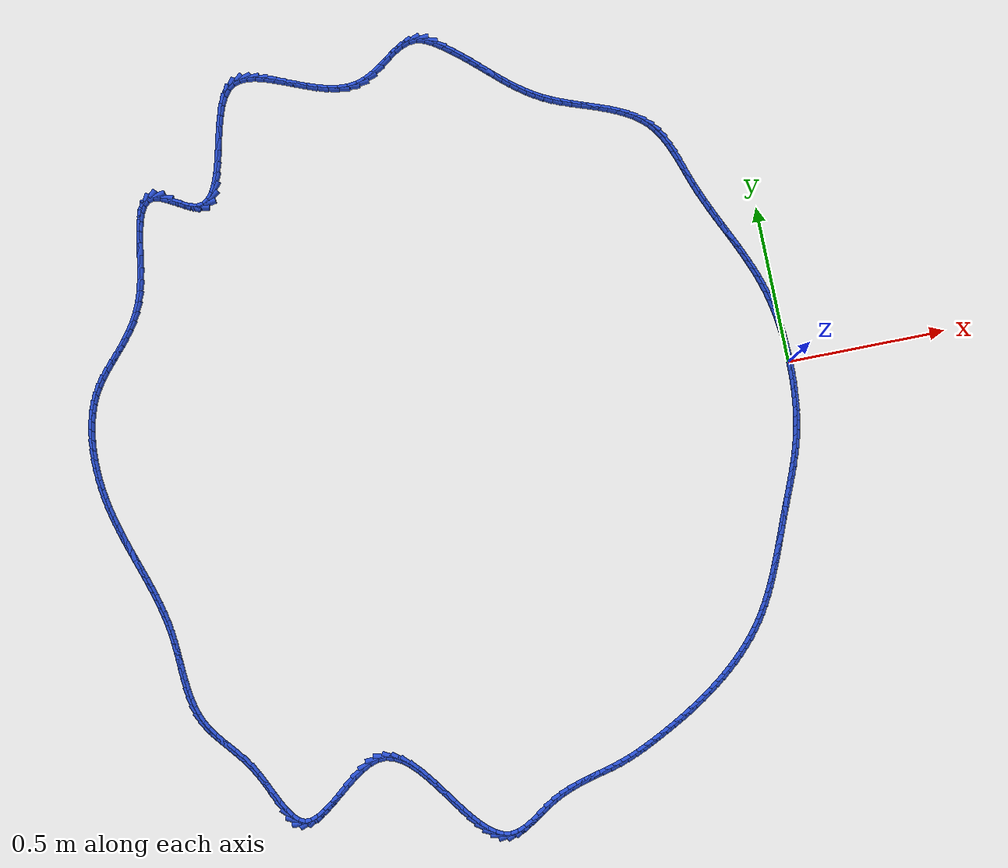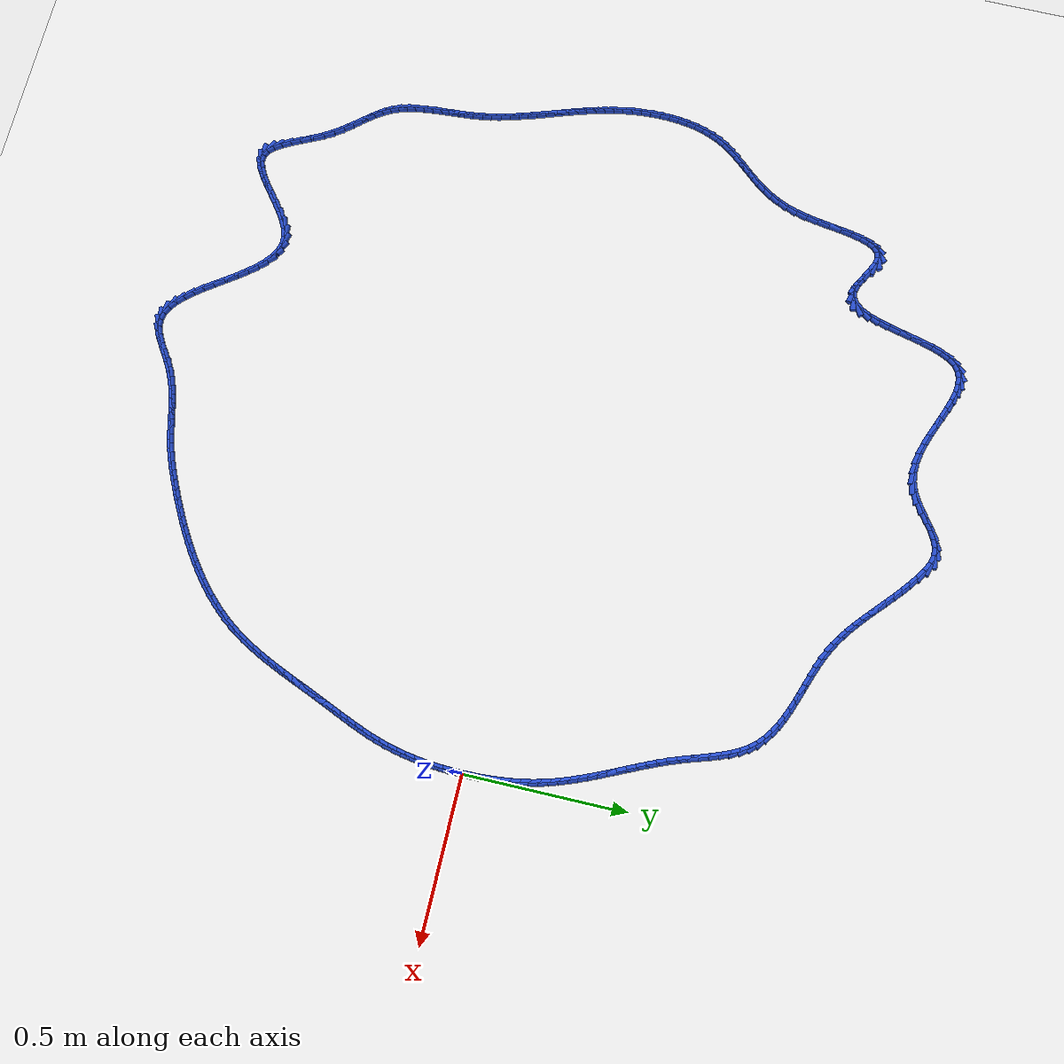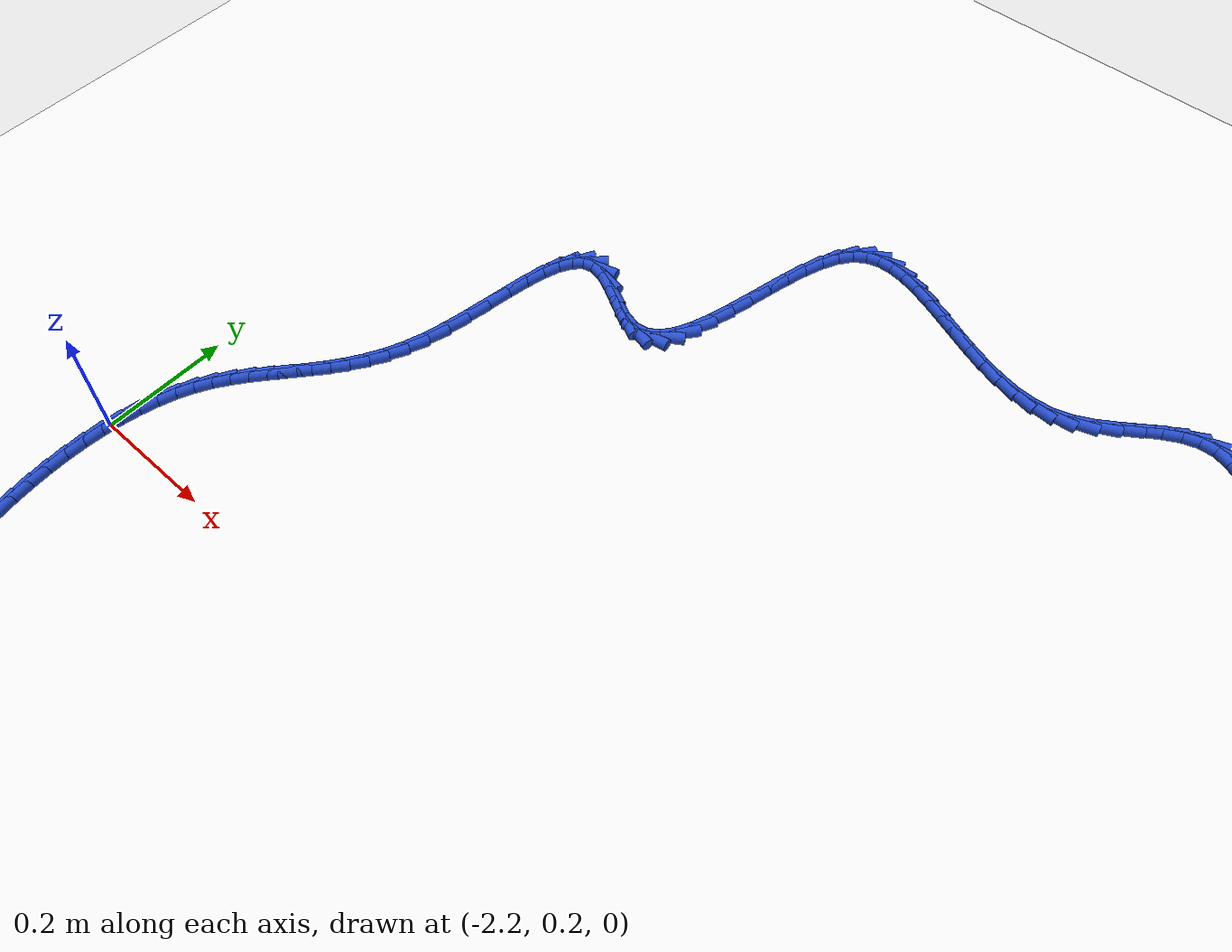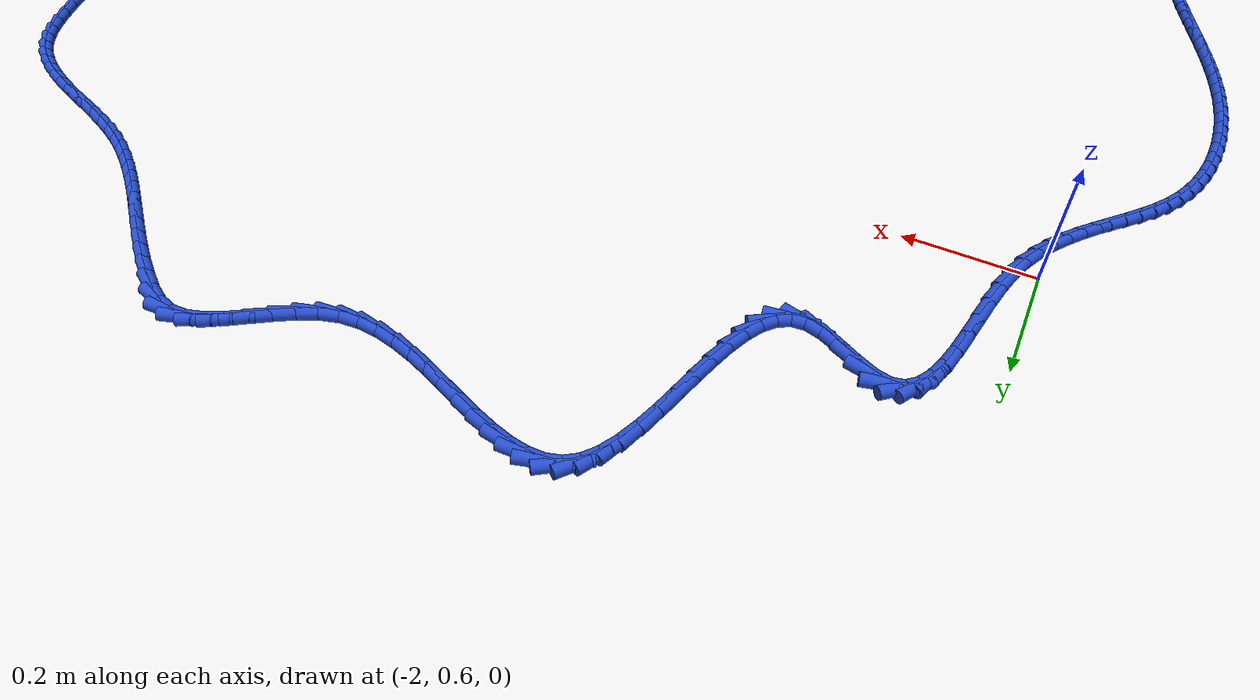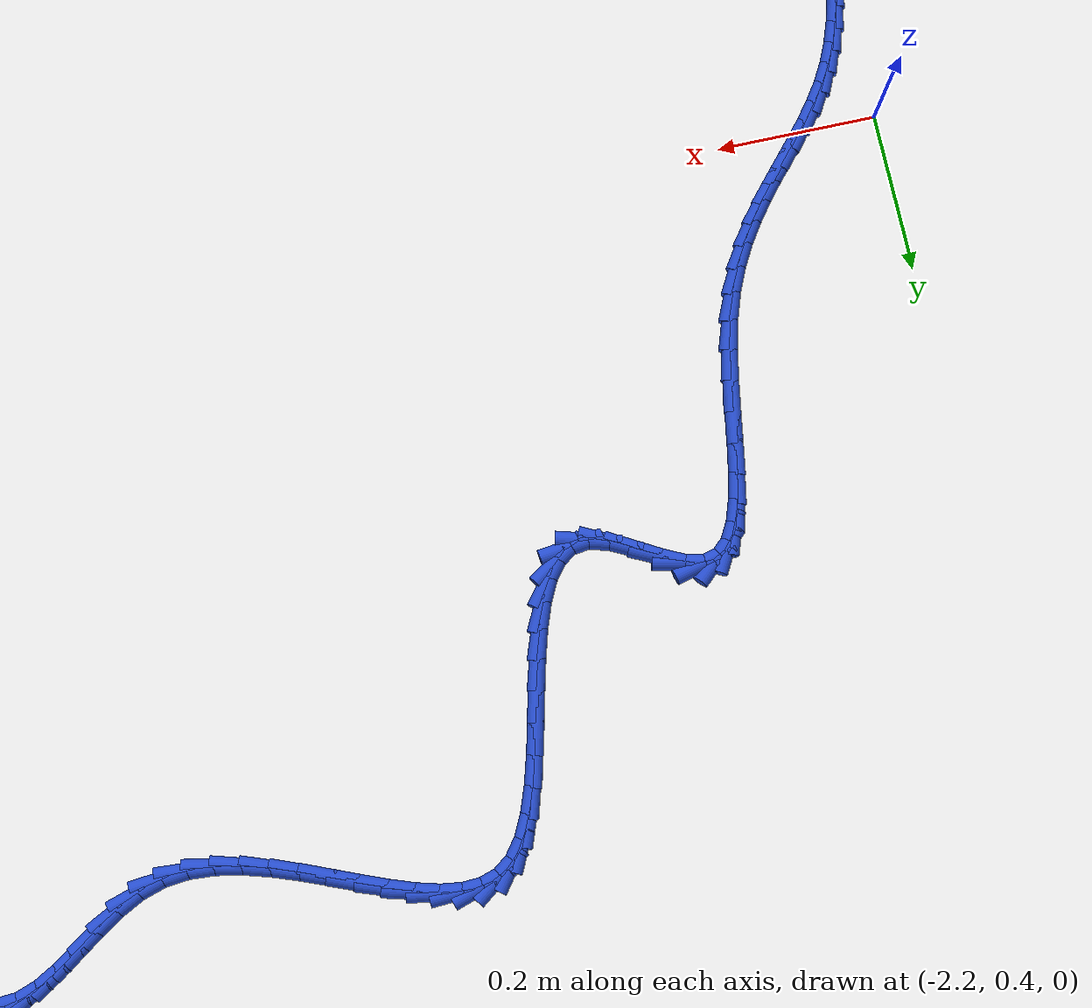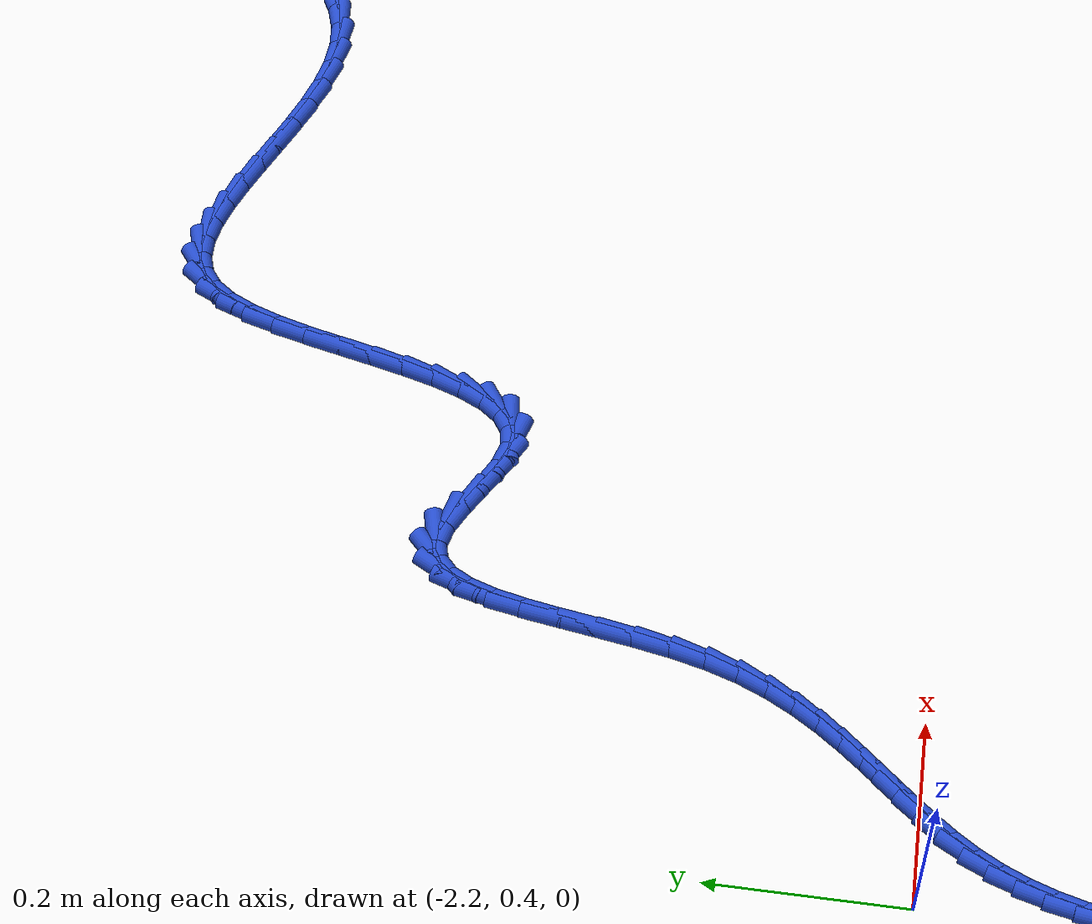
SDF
<sdf version="1.6">
 <world name="default">
  <light name="sun" type="directional">
   <pose>0 0 10 0 -0 0</pose>
   <diffuse>0.8 0.8 0.8 1</diffuse>
   <specular>0.2 0.2 0.2 1</specular>
   <attenuation>
    <range>1000</range>
    <constant>0.9</constant>
    <linear>0.01</linear>
    <quadratic>0.001</quadratic>
   </attenuation>
   <direction>-0.5 0.1 -0.9</direction>
  </light>
  <model name="ground_plane">
   <static>1</static>
   <link name="link">
    <collision name="collision">
     <geometry><plane><normal>0 0 1</normal><size>100 100</size></plane></geometry>
     <surface><friction><ode><mu>100</mu><mu2>50</mu2></ode></friction></surface>
    </collision>
    <visual name="visual">
     <cast_shadows>0</cast_shadows>
     <geometry><plane><normal>0 0 1</normal><size>100 100</size></plane></geometry>
     <material>
      <script><uri>file://media/materials/scripts/gazebo.material</uri><name>Gazebo/WhiteGlow</name></script>
     </material>
    </visual>
   </link>
  </model>
  <gravity>0 0 -9.8</gravity>
  <magnetic_field>6e-06 2.3e-05 -4.2e-05</magnetic_field>
  <atmosphere type="adiabatic"/>
  <physics name="default_physics" default="0" type="ode">
   <max_step_size>0.001</max_step_size>
   <real_time_factor>1</real_time_factor>
   <real_time_update_rate>1000</real_time_update_rate>
  </physics>
  <scene><ambient>0.4 0.4 0.4 1</ambient><background>0.7 0.7 0.7 1</background><shadows>1</shadows></scene>
  <spherical_coordinates>
   <surface_model>EARTH_WGS84</surface_model>
   <latitude_deg>0</latitude_deg>
   <longitude_deg>0</longitude_deg>
   <elevation>0</elevation>
   <heading_deg>0</heading_deg>
  </spherical_coordinates>
  <model name="line">
   <link name="link_0">
    <pose>9.974659986866641e-18 1.3877787807814457e-17 0.01 0 1.57 -1.5580215021188153</pose>
    <collision name="collision">
     <geometry><cylinder><radius>0.01</radius><length>0.08</length></cylinder></geometry>
    </collision>
    <visual name="visual">
     <material>
      <script><name>Gazebo/Blue</name><uri>file://media/materials/scripts/gazebo.material</uri></script>
     </material>
     <geometry><cylinder><radius>0.01</radius><length>0.08</length></cylinder></geometry>
    </visual>
   </link>
   <link name="link_1">
    <pose>-0.00037993314938865845 0.029739154228859945 0.01 0 1.57 -1.5317703661067583</pose>
    <collision name="collision">
     <geometry><cylinder><radius>0.01</radius><length>0.08</length></cylinder></geometry>
    </collision>
    <visual name="visual">
     <material>
      <script><name>Gazebo/Blue</name><uri>file://media/materials/scripts/gazebo.material</uri></script>
     </material>
     <geometry><cylinder><radius>0.01</radius><length>0.08</length></cylinder></geometry>
    </visual>
   </link>
   <link name="link_2">
    <pose>-0.0015398807395258156 0.05944652422735148 0.01 0 1.57 -1.5037752928353882</pose>
    <collision name="collision">
     <geometry><cylinder><radius>0.01</radius><length>0.08</length></cylinder></geometry>
    </collision>
    <visual name="visual">
     <material>
      <script><name>Gazebo/Blue</name><uri>file://media/materials/scripts/gazebo.material</uri></script>
     </material>
     <geometry><cylinder><radius>0.01</radius><length>0.08</length></cylinder></geometry>
    </visual>
   </link>
   <link name="link_3">
    <pose>-0.0035278272089784113 0.08906363040889238 0.01 0 1.57 -1.4739139944669084</pose>
    <collision name="collision">
     <geometry><cylinder><radius>0.01</radius><length>0.08</length></cylinder></geometry>
    </collision>
    <visual name="visual">
     <material>
      <script><name>Gazebo/Blue</name><uri>file://media/materials/scripts/gazebo.material</uri></script>
     </material>
     <geometry><cylinder><radius>0.01</radius><length>0.08</length></cylinder></geometry>
    </visual>
   </link>
   <link name="link_4">
    <pose>-0.006391756996313396 0.11853199318690044 0.01 0 1.57 -1.4420607749533236</pose>
    <collision name="collision">
     <geometry><cylinder><radius>0.01</radius><length>0.08</length></cylinder></geometry>
    </collision>
    <visual name="visual">
     <material>
      <script><name>Gazebo/Blue</name><uri>file://media/materials/scripts/gazebo.material</uri></script>
     </material>
     <geometry><cylinder><radius>0.01</radius><length>0.08</length></cylinder></geometry>
    </visual>
   </link>
   <link name="link_5">
    <pose>-0.010179654540097727 0.1477931329747935 0.01 0 1.57 -1.4080889400098242</pose>
    <collision name="collision">
     <geometry><cylinder><radius>0.01</radius><length>0.08</length></cylinder></geometry>
    </collision>
    <visual name="visual">
     <material>
      <script><name>Gazebo/Blue</name><uri>file://media/materials/scripts/gazebo.material</uri></script>
     </material>
     <geometry><cylinder><radius>0.01</radius><length>0.08</length></cylinder></geometry>
    </visual>
   </link>
   <link name="link_6">
    <pose>-0.014939504278898352 0.1767885701859893 0.01 0 1.57 -1.3718741298951571</pose>
    <collision name="collision">
     <geometry><cylinder><radius>0.01</radius><length>0.08</length></cylinder></geometry>
    </collision>
    <visual name="visual">
     <material>
      <script><name>Gazebo/Blue</name><uri>file://media/materials/scripts/gazebo.material</uri></script>
     </material>
     <geometry><cylinder><radius>0.01</radius><length>0.08</length></cylinder></geometry>
    </visual>
   </link>
   <link name="link_7">
    <pose>-0.020719290651282217 0.20545982523390566 0.01 0 1.57 -1.3332987570523114</pose>
    <collision name="collision">
     <geometry><cylinder><radius>0.01</radius><length>0.08</length></cylinder></geometry>
    </collision>
    <visual name="visual">
     <material>
      <script><name>Gazebo/Blue</name><uri>file://media/materials/scripts/gazebo.material</uri></script>
     </material>
     <geometry><cylinder><radius>0.01</radius><length>0.08</length></cylinder></geometry>
    </visual>
   </link>
   <link name="link_8">
    <pose>-0.027566998095816288 0.23374841853196038 0.01 0 1.57 -1.292880538222184</pose>
    <collision name="collision">
     <geometry><cylinder><radius>0.01</radius><length>0.08</length></cylinder></geometry>
    </collision>
    <visual name="visual">
     <material>
      <script><name>Gazebo/Blue</name><uri>file://media/materials/scripts/gazebo.material</uri></script>
     </material>
     <geometry><cylinder><radius>0.01</radius><length>0.08</length></cylinder></geometry>
    </visual>
   </link>
   <link name="link_9">
    <pose>-0.03551507415191414 0.26160716528374955 0.01 0 1.57 -1.2552306841127459</pose>
    <collision name="collision">
     <geometry><cylinder><radius>0.01</radius><length>0.08</length></cylinder></geometry>
    </collision>
    <visual name="visual">
     <material>
      <script><name>Gazebo/Blue</name><uri>file://media/materials/scripts/gazebo.material</uri></script>
     </material>
     <geometry><cylinder><radius>0.01</radius><length>0.08</length></cylinder></geometry>
    </visual>
   </link>
   <link name="link_10">
    <pose>-0.04448165666233696 0.2890719799024542 0.01 0 1.57 -1.222621313202481</pose>
    <collision name="collision">
     <geometry><cylinder><radius>0.01</radius><length>0.08</length></cylinder></geometry>
    </collision>
    <visual name="visual">
     <material>
      <script><name>Gazebo/Blue</name><uri>file://media/materials/scripts/gazebo.material</uri></script>
     </material>
     <geometry><cylinder><radius>0.01</radius><length>0.08</length></cylinder></geometry>
    </visual>
   </link>
   <link name="link_11">
    <pose>-0.05433385140377356 0.3162158753543811 0.01 0 1.57 -1.1952288255123313</pose>
    <collision name="collision">
     <geometry><cylinder><radius>0.01</radius><length>0.08</length></cylinder></geometry>
    </collision>
    <visual name="visual">
     <material>
      <script><name>Gazebo/Blue</name><uri>file://media/materials/scripts/gazebo.material</uri></script>
     </material>
     <geometry><cylinder><radius>0.01</radius><length>0.08</length></cylinder></geometry>
    </visual>
   </link>
   <link name="link_12">
    <pose>-0.064938527730413 0.3431120364768459 0.01 0 1.57 -1.1731381027281085</pose>
    <collision name="collision">
     <geometry><cylinder><radius>0.01</radius><length>0.08</length></cylinder></geometry>
    </collision>
    <visual name="visual">
     <material>
      <script><name>Gazebo/Blue</name><uri>file://media/materials/scripts/gazebo.material</uri></script>
     </material>
     <geometry><cylinder><radius>0.01</radius><length>0.08</length></cylinder></geometry>
    </visual>
   </link>
   <link name="link_13">
    <pose>-0.07616255499644435 0.36983364810716435 0.01 0 1.57 -1.1563732066569763</pose>
    <collision name="collision">
     <geometry><cylinder><radius>0.01</radius><length>0.08</length></cylinder></geometry>
    </collision>
    <visual name="visual">
     <material>
      <script><name>Gazebo/Blue</name><uri>file://media/materials/scripts/gazebo.material</uri></script>
     </material>
     <geometry><cylinder><radius>0.01</radius><length>0.08</length></cylinder></geometry>
    </visual>
   </link>
   <link name="link_14">
    <pose>-0.08787280255605667 0.39645389508265183 0.01 0 1.57 -1.1449160118824349</pose>
    <collision name="collision">
     <geometry><cylinder><radius>0.01</radius><length>0.08</length></cylinder></geometry>
    </collision>
    <visual name="visual">
     <material>
      <script><name>Gazebo/Blue</name><uri>file://media/materials/scripts/gazebo.material</uri></script>
     </material>
     <geometry><cylinder><radius>0.01</radius><length>0.08</length></cylinder></geometry>
    </visual>
   </link>
   <link name="link_15">
    <pose>-0.09993613976343904 0.42304596224062396 0.01 0 1.57 -1.1387209045980469</pose>
    <collision name="collision">
     <geometry><cylinder><radius>0.01</radius><length>0.08</length></cylinder></geometry>
    </collision>
    <visual name="visual">
     <material>
      <script><name>Gazebo/Blue</name><uri>file://media/materials/scripts/gazebo.material</uri></script>
     </material>
     <geometry><cylinder><radius>0.01</radius><length>0.08</length></cylinder></geometry>
    </visual>
   </link>
   <link name="link_16">
    <pose>-0.1122194359727805 0.44968303441839635 0.01 0 1.57 -1.1377249940676806</pose>
    <collision name="collision">
     <geometry><cylinder><radius>0.01</radius><length>0.08</length></cylinder></geometry>
    </collision>
    <visual name="visual">
     <material>
      <script><name>Gazebo/Blue</name><uri>file://media/materials/scripts/gazebo.material</uri></script>
     </material>
     <geometry><cylinder><radius>0.01</radius><length>0.08</length></cylinder></geometry>
    </visual>
   </link>
   <link name="link_17">
    <pose>-0.12458956053827015 0.47643829645328467 0.01 0 1.57 -1.141853790209345</pose>
    <collision name="collision">
     <geometry><cylinder><radius>0.01</radius><length>0.08</length></cylinder></geometry>
    </collision>
    <visual name="visual">
     <material>
      <script><name>Gazebo/Blue</name><uri>file://media/materials/scripts/gazebo.material</uri></script>
     </material>
     <geometry><cylinder><radius>0.01</radius><length>0.08</length></cylinder></geometry>
    </visual>
   </link>
   <link name="link_18">
    <pose>-0.13691338281409704 0.5033849331826044 0.01 0 1.57 -1.1510225858339869</pose>
    <collision name="collision">
     <geometry><cylinder><radius>0.01</radius><length>0.08</length></cylinder></geometry>
    </collision>
    <visual name="visual">
     <material>
      <script><name>Gazebo/Blue</name><uri>file://media/materials/scripts/gazebo.material</uri></script>
     </material>
     <geometry><cylinder><radius>0.01</radius><length>0.08</length></cylinder></geometry>
    </visual>
   </link>
   <link name="link_19">
    <pose>-0.1490577721544502 0.530596129443671 0.01 0 1.57 -1.1651339357890707</pose>
    <collision name="collision">
     <geometry><cylinder><radius>0.01</radius><length>0.08</length></cylinder></geometry>
    </collision>
    <visual name="visual">
     <material>
      <script><name>Gazebo/Blue</name><uri>file://media/materials/scripts/gazebo.material</uri></script>
     </material>
     <geometry><cylinder><radius>0.01</radius><length>0.08</length></cylinder></geometry>
    </visual>
   </link>
   <link name="link_20">
    <pose>-0.16088959791351878 0.5581450700738003 0.01 0 1.57 -1.1840717364077593</pose>
    <collision name="collision">
     <geometry><cylinder><radius>0.01</radius><length>0.08</length></cylinder></geometry>
    </collision>
    <visual name="visual">
     <material>
      <script><name>Gazebo/Blue</name><uri>file://media/materials/scripts/gazebo.material</uri></script>
     </material>
     <geometry><cylinder><radius>0.01</radius><length>0.08</length></cylinder></geometry>
    </visual>
   </link>
   <link name="link_21">
    <pose>-0.1722757294454918 0.5861049399103078 0.01 0 1.57 -1.2076925482630207</pose>
    <collision name="collision">
     <geometry><cylinder><radius>0.01</radius><length>0.08</length></cylinder></geometry>
    </collision>
    <visual name="visual">
     <material>
      <script><name>Gazebo/Blue</name><uri>file://media/materials/scripts/gazebo.material</uri></script>
     </material>
     <geometry><cylinder><radius>0.01</radius><length>0.08</length></cylinder></geometry>
    </visual>
   </link>
   <link name="link_22">
    <pose>-0.1830830361045583 0.6145489237905091 0.01 0 1.57 -1.2336070755049982</pose>
    <collision name="collision">
     <geometry><cylinder><radius>0.01</radius><length>0.08</length></cylinder></geometry>
    </collision>
    <visual name="visual">
     <material>
      <script><name>Gazebo/Blue</name><uri>file://media/materials/scripts/gazebo.material</uri></script>
     </material>
     <geometry><cylinder><radius>0.01</radius><length>0.08</length></cylinder></geometry>
    </visual>
   </link>
   <link name="link_23">
    <pose>-0.19323381619091404 0.6435033733119847 0.01 0 1.57 -1.246749932868883</pose>
    <collision name="collision">
     <geometry><cylinder><radius>0.01</radius><length>0.08</length></cylinder></geometry>
    </collision>
    <visual name="visual">
     <material>
      <script><name>Gazebo/Blue</name><uri>file://media/materials/scripts/gazebo.material</uri></script>
     </material>
     <geometry><cylinder><radius>0.01</radius><length>0.08</length></cylinder></geometry>
    </visual>
   </link>
   <link name="link_24">
    <pose>-0.20303139236991724 0.6726727034900045 0.01 0 1.57 -1.2410851200930193</pose>
    <collision name="collision">
     <geometry><cylinder><radius>0.01</radius><length>0.08</length></cylinder></geometry>
    </collision>
    <visual name="visual">
     <material>
      <script><name>Gazebo/Blue</name><uri>file://media/materials/scripts/gazebo.material</uri></script>
     </material>
     <geometry><cylinder><radius>0.01</radius><length>0.08</length></cylinder></geometry>
    </visual>
   </link>
   <link name="link_25">
    <pose>-0.2129392703352618 0.701625986875152 0.01 0 1.57 -1.2161343185415425</pose>
    <collision name="collision">
     <geometry><cylinder><radius>0.01</radius><length>0.08</length></cylinder></geometry>
    </collision>
    <visual name="visual">
     <material>
      <script><name>Gazebo/Blue</name><uri>file://media/materials/scripts/gazebo.material</uri></script>
     </material>
     <geometry><cylinder><radius>0.01</radius><length>0.08</length></cylinder></geometry>
    </visual>
   </link>
   <link name="link_26">
    <pose>-0.2234215102208193 0.7299318275582686 0.01 0 1.57 -1.1705075194769952</pose>
    <collision name="collision">
     <geometry><cylinder><radius>0.01</radius><length>0.08</length></cylinder></geometry>
    </collision>
    <visual name="visual">
     <material>
      <script><name>Gazebo/Blue</name><uri>file://media/materials/scripts/gazebo.material</uri></script>
     </material>
     <geometry><cylinder><radius>0.01</radius><length>0.08</length></cylinder></geometry>
    </visual>
   </link>
   <link name="link_27">
    <pose>-0.23494217216046115 0.7571588296301952 0.01 0 1.57 -1.1020364806004668</pose>
    <collision name="collision">
     <geometry><cylinder><radius>0.01</radius><length>0.08</length></cylinder></geometry>
    </collision>
    <visual name="visual">
     <material>
      <script><name>Gazebo/Blue</name><uri>file://media/materials/scripts/gazebo.material</uri></script>
     </material>
     <geometry><cylinder><radius>0.01</radius><length>0.08</length></cylinder></geometry>
    </visual>
   </link>
   <link name="link_28">
    <pose>-0.24796531628805887 0.7828755971817736 0.01 0 1.57 -1.0082679053842776</pose>
    <collision name="collision">
     <geometry><cylinder><radius>0.01</radius><length>0.08</length></cylinder></geometry>
    </collision>
    <visual name="visual">
     <material>
      <script><name>Gazebo/Blue</name><uri>file://media/materials/scripts/gazebo.material</uri></script>
     </material>
     <geometry><cylinder><radius>0.01</radius><length>0.08</length></cylinder></geometry>
    </visual>
   </link>
   <link name="link_29">
    <pose>-0.26295500273748396 0.8066507343038446 0.01 0 1.57 -0.8877111569736988</pose>
    <collision name="collision">
     <geometry><cylinder><radius>0.01</radius><length>0.08</length></cylinder></geometry>
    </collision>
    <visual name="visual">
     <material>
      <script><name>Gazebo/Blue</name><uri>file://media/materials/scripts/gazebo.material</uri></script>
     </material>
     <geometry><cylinder><radius>0.01</radius><length>0.08</length></cylinder></geometry>
    </visual>
   </link>
   <link name="link_30">
    <pose>-0.2803731900068053 0.8280548673200155 0.01 0 1.57 -0.7544953234870238</pose>
    <collision name="collision">
     <geometry><cylinder><radius>0.01</radius><length>0.08</length></cylinder></geometry>
    </collision>
    <visual name="visual">
     <material>
      <script><name>Gazebo/Blue</name><uri>file://media/materials/scripts/gazebo.material</uri></script>
     </material>
     <geometry><cylinder><radius>0.01</radius><length>0.08</length></cylinder></geometry>
    </visual>
   </link>
   <link name="link_31">
    <pose>-0.30042584895691915 0.8469049385839321 0.01 0 1.57 -0.6376440695467996</pose>
    <collision name="collision">
     <geometry><cylinder><radius>0.01</radius><length>0.08</length></cylinder></geometry>
    </collision>
    <visual name="visual">
     <material>
      <script><name>Gazebo/Blue</name><uri>file://media/materials/scripts/gazebo.material</uri></script>
     </material>
     <geometry><cylinder><radius>0.01</radius><length>0.08</length></cylinder></geometry>
    </visual>
   </link>
   <link name="link_32">
    <pose>-0.3228208729654477 0.8634971497981951 0.01 0 1.57 -0.5420153672627641</pose>
    <collision name="collision">
     <geometry><cylinder><radius>0.01</radius><length>0.08</length></cylinder></geometry>
    </collision>
    <visual name="visual">
     <material>
      <script><name>Gazebo/Blue</name><uri>file://media/materials/scripts/gazebo.material</uri></script>
     </material>
     <geometry><cylinder><radius>0.01</radius><length>0.08</length></cylinder></geometry>
    </visual>
   </link>
   <link name="link_33">
    <pose>-0.34720880208213806 0.8781828890962331 0.01 0 1.57 -0.4671745885433363</pose>
    <collision name="collision">
     <geometry><cylinder><radius>0.01</radius><length>0.08</length></cylinder></geometry>
    </collision>
    <visual name="visual">
     <material>
      <script><name>Gazebo/Blue</name><uri>file://media/materials/scripts/gazebo.material</uri></script>
     </material>
     <geometry><cylinder><radius>0.01</radius><length>0.08</length></cylinder></geometry>
    </visual>
   </link>
   <link name="link_34">
    <pose>-0.37324017635673806 0.8913135446114747 0.01 0 1.57 -0.411553588994451</pose>
    <collision name="collision">
     <geometry><cylinder><radius>0.01</radius><length>0.08</length></cylinder></geometry>
    </collision>
    <visual name="visual">
     <material>
      <script><name>Gazebo/Blue</name><uri>file://media/materials/scripts/gazebo.material</uri></script>
     </material>
     <geometry><cylinder><radius>0.01</radius><length>0.08</length></cylinder></geometry>
    </visual>
   </link>
   <link name="link_35">
    <pose>-0.400565535838995 0.903240504477349 0.01 0 1.57 -0.37337183882803654</pose>
    <collision name="collision">
     <geometry><cylinder><radius>0.01</radius><length>0.08</length></cylinder></geometry>
    </collision>
    <visual name="visual">
     <material>
      <script><name>Gazebo/Blue</name><uri>file://media/materials/scripts/gazebo.material</uri></script>
     </material>
     <geometry><cylinder><radius>0.01</radius><length>0.08</length></cylinder></geometry>
    </visual>
   </link>
   <link name="link_36">
    <pose>-0.42883542057865603 0.914315156827284 0.01 0 1.57 -0.3511368698114904</pose>
    <collision name="collision">
     <geometry><cylinder><radius>0.01</radius><length>0.08</length></cylinder></geometry>
    </collision>
    <visual name="visual">
     <material>
      <script><name>Gazebo/Blue</name><uri>file://media/materials/scripts/gazebo.material</uri></script>
     </material>
     <geometry><cylinder><radius>0.01</radius><length>0.08</length></cylinder></geometry>
    </visual>
   </link>
   <link name="link_37">
    <pose>-0.4577003706254688 0.9248888897947083 0.01 0 1.57 -0.3438637776267611</pose>
    <collision name="collision">
     <geometry><cylinder><radius>0.01</radius><length>0.08</length></cylinder></geometry>
    </collision>
    <visual name="visual">
     <material>
      <script><name>Gazebo/Blue</name><uri>file://media/materials/scripts/gazebo.material</uri></script>
     </material>
     <geometry><cylinder><radius>0.01</radius><length>0.08</length></cylinder></geometry>
    </visual>
   </link>
   <link name="link_38">
    <pose>-0.48681092602918086 0.9353130915130508 0.01 0 1.57 -0.35114902409987375</pose>
    <collision name="collision">
     <geometry><cylinder><radius>0.01</radius><length>0.08</length></cylinder></geometry>
    </collision>
    <visual name="visual">
     <material>
      <script><name>Gazebo/Blue</name><uri>file://media/materials/scripts/gazebo.material</uri></script>
     </material>
     <geometry><cylinder><radius>0.01</radius><length>0.08</length></cylinder></geometry>
    </visual>
   </link>
   <link name="link_39">
    <pose>-0.5158176268395396 0.9459391501157397 0.01 0 1.57 -0.37317720943024635</pose>
    <collision name="collision">
     <geometry><cylinder><radius>0.01</radius><length>0.08</length></cylinder></geometry>
    </collision>
    <visual name="visual">
     <material>
      <script><name>Gazebo/Blue</name><uri>file://media/materials/scripts/gazebo.material</uri></script>
     </material>
     <geometry><cylinder><radius>0.01</radius><length>0.08</length></cylinder></geometry>
    </visual>
   </link>
   <link name="link_40">
    <pose>-0.5443710131062921 0.9571184537362042 0.01 0 1.57 -0.41068645798672754</pose>
    <collision name="collision">
     <geometry><cylinder><radius>0.01</radius><length>0.08</length></cylinder></geometry>
    </collision>
    <visual name="visual">
     <material>
      <script><name>Gazebo/Blue</name><uri>file://media/materials/scripts/gazebo.material</uri></script>
     </material>
     <geometry><cylinder><radius>0.01</radius><length>0.08</length></cylinder></geometry>
    </visual>
   </link>
   <link name="link_41">
    <pose>-0.5721216248791862 0.9692023905078724 0.01 0 1.57 -0.4648060281750025</pose>
    <collision name="collision">
     <geometry><cylinder><radius>0.01</radius><length>0.08</length></cylinder></geometry>
    </collision>
    <visual name="visual">
     <material>
      <script><name>Gazebo/Blue</name><uri>file://media/materials/scripts/gazebo.material</uri></script>
     </material>
     <geometry><cylinder><radius>0.01</radius><length>0.08</length></cylinder></geometry>
    </visual>
   </link>
   <link name="link_42">
    <pose>-0.5987215316499668 0.9825408835355761 0.01 0 1.57 -0.5288140786739194</pose>
    <collision name="collision">
     <geometry><cylinder><radius>0.01</radius><length>0.08</length></cylinder></geometry>
    </collision>
    <visual name="visual">
     <material>
      <script><name>Gazebo/Blue</name><uri>file://media/materials/scripts/gazebo.material</uri></script>
     </material>
     <geometry><cylinder><radius>0.01</radius><length>0.08</length></cylinder></geometry>
    </visual>
   </link>
   <link name="link_43">
    <pose>-0.6240015531233065 0.9973126338876024 0.01 0 1.57 -0.5869843435602776</pose>
    <collision name="collision">
     <geometry><cylinder><radius>0.01</radius><length>0.08</length></cylinder></geometry>
    </collision>
    <visual name="visual">
     <material>
      <script><name>Gazebo/Blue</name><uri>file://media/materials/scripts/gazebo.material</uri></script>
     </material>
     <geometry><cylinder><radius>0.01</radius><length>0.08</length></cylinder></geometry>
    </visual>
   </link>
   <link name="link_44">
    <pose>-0.6481363241935962 1.0133670074330503 0.01 0 1.57 -0.6364742065862207</pose>
    <collision name="collision">
     <geometry><cylinder><radius>0.01</radius><length>0.08</length></cylinder></geometry>
    </collision>
    <visual name="visual">
     <material>
      <script><name>Gazebo/Blue</name><uri>file://media/materials/scripts/gazebo.material</uri></script>
     </material>
     <geometry><cylinder><radius>0.01</radius><length>0.08</length></cylinder></geometry>
    </visual>
   </link>
   <link name="link_45">
    <pose>-0.6713395191528839 1.0305159748118744 0.01 0 1.57 -0.676563248699346</pose>
    <collision name="collision">
     <geometry><cylinder><radius>0.01</radius><length>0.08</length></cylinder></geometry>
    </collision>
    <visual name="visual">
     <material>
      <script><name>Gazebo/Blue</name><uri>file://media/materials/scripts/gazebo.material</uri></script>
     </material>
     <geometry><cylinder><radius>0.01</radius><length>0.08</length></cylinder></geometry>
    </visual>
   </link>
   <link name="link_46">
    <pose>-0.6938248122932177 1.0485715066640293 0.01 0 1.57 -0.7068705362299524</pose>
    <collision name="collision">
     <geometry><cylinder><radius>0.01</radius><length>0.08</length></cylinder></geometry>
    </collision>
    <visual name="visual">
     <material>
      <script><name>Gazebo/Blue</name><uri>file://media/materials/scripts/gazebo.material</uri></script>
     </material>
     <geometry><cylinder><radius>0.01</radius><length>0.08</length></cylinder></geometry>
    </visual>
   </link>
   <link name="link_47">
    <pose>-0.715805877906645 1.0673455736294688 0.01 0 1.57 -0.7272631176615374</pose>
    <collision name="collision">
     <geometry><cylinder><radius>0.01</radius><length>0.08</length></cylinder></geometry>
    </collision>
    <visual name="visual">
     <material>
      <script><name>Gazebo/Blue</name><uri>file://media/materials/scripts/gazebo.material</uri></script>
     </material>
     <geometry><cylinder><radius>0.01</radius><length>0.08</length></cylinder></geometry>
    </visual>
   </link>
   <link name="link_48">
    <pose>-0.7374963902852139 1.0866501463481475 0.01 0 1.57 -0.7377717776666011</pose>
    <collision name="collision">
     <geometry><cylinder><radius>0.01</radius><length>0.08</length></cylinder></geometry>
    </collision>
    <visual name="visual">
     <material>
      <script><name>Gazebo/Blue</name><uri>file://media/materials/scripts/gazebo.material</uri></script>
     </material>
     <geometry><cylinder><radius>0.01</radius><length>0.08</length></cylinder></geometry>
    </visual>
   </link>
   <link name="link_49">
    <pose>-0.7591100237209718 1.1062971954600191 0.01 0 1.57 -0.7385289666817251</pose>
    <collision name="collision">
     <geometry><cylinder><radius>0.01</radius><length>0.08</length></cylinder></geometry>
    </collision>
    <visual name="visual">
     <material>
      <script><name>Gazebo/Blue</name><uri>file://media/materials/scripts/gazebo.material</uri></script>
     </material>
     <geometry><cylinder><radius>0.01</radius><length>0.08</length></cylinder></geometry>
    </visual>
   </link>
   <link name="link_50">
    <pose>-0.7808604525059676 1.1260986916050388 0.01 0 1.57 -0.7297344261502884</pose>
    <collision name="collision">
     <geometry><cylinder><radius>0.01</radius><length>0.08</length></cylinder></geometry>
    </collision>
    <visual name="visual">
     <material>
      <script><name>Gazebo/Blue</name><uri>file://media/materials/scripts/gazebo.material</uri></script>
     </material>
     <geometry><cylinder><radius>0.01</radius><length>0.08</length></cylinder></geometry>
    </visual>
   </link>
   <link name="link_51">
    <pose>-0.8029613509322482 1.14586660542316 0.01 0 1.57 -0.7116482299649388</pose>
    <collision name="collision">
     <geometry><cylinder><radius>0.01</radius><length>0.08</length></cylinder></geometry>
    </collision>
    <visual name="visual">
     <material>
      <script><name>Gazebo/Blue</name><uri>file://media/materials/scripts/gazebo.material</uri></script>
     </material>
     <geometry><cylinder><radius>0.01</radius><length>0.08</length></cylinder></geometry>
    </visual>
   </link>
   <link name="link_52">
    <pose>-0.8256263932918614 1.1654129075543374 0.01 0 1.57 -0.6846077449265867</pose>
    <collision name="collision">
     <geometry><cylinder><radius>0.01</radius><length>0.08</length></cylinder></geometry>
    </collision>
    <visual name="visual">
     <material>
      <script><name>Gazebo/Blue</name><uri>file://media/materials/scripts/gazebo.material</uri></script>
     </material>
     <geometry><cylinder><radius>0.01</radius><length>0.08</length></cylinder></geometry>
    </visual>
   </link>
   <link name="link_53">
    <pose>-0.8490692538768555 1.1845495686385252 0.01 0 1.57 -0.6490627013791429</pose>
    <collision name="collision">
     <geometry><cylinder><radius>0.01</radius><length>0.08</length></cylinder></geometry>
    </collision>
    <visual name="visual">
     <material>
      <script><name>Gazebo/Blue</name><uri>file://media/materials/scripts/gazebo.material</uri></script>
     </material>
     <geometry><cylinder><radius>0.01</radius><length>0.08</length></cylinder></geometry>
    </visual>
   </link>
   <link name="link_54">
    <pose>-0.8735036069792784 1.203088559315678 0.01 0 1.57 -0.6025146676400259</pose>
    <collision name="collision">
     <geometry><cylinder><radius>0.01</radius><length>0.08</length></cylinder></geometry>
    </collision>
    <visual name="visual">
     <material>
      <script><name>Gazebo/Blue</name><uri>file://media/materials/scripts/gazebo.material</uri></script>
     </material>
     <geometry><cylinder><radius>0.01</radius><length>0.08</length></cylinder></geometry>
    </visual>
   </link>
   <link name="link_55">
    <pose>-0.8991029577073367 1.2206966840842806 0.01 0 1.57 -0.49761944474961695</pose>
    <collision name="collision">
     <geometry><cylinder><radius>0.01</radius><length>0.08</length></cylinder></geometry>
    </collision>
    <visual name="visual">
     <material>
      <script><name>Gazebo/Blue</name><uri>file://media/materials/scripts/gazebo.material</uri></script>
     </material>
     <geometry><cylinder><radius>0.01</radius><length>0.08</length></cylinder></geometry>
    </visual>
   </link>
   <link name="link_56">
    <pose>-0.9254835992125153 1.2350270567973185 0.01 0 1.57 -0.2682205913940863</pose>
    <collision name="collision">
     <geometry><cylinder><radius>0.01</radius><length>0.08</length></cylinder></geometry>
    </collision>
    <visual name="visual">
     <material>
      <script><name>Gazebo/Blue</name><uri>file://media/materials/scripts/gazebo.material</uri></script>
     </material>
     <geometry><cylinder><radius>0.01</radius><length>0.08</length></cylinder></geometry>
    </visual>
   </link>
   <link name="link_57">
    <pose>-0.9518570570471334 1.2422756269401118 0.01 0 1.57 0.06903926567369674</pose>
    <collision name="collision">
     <geometry><cylinder><radius>0.01</radius><length>0.08</length></cylinder></geometry>
    </collision>
    <visual name="visual">
     <material>
      <script><name>Gazebo/Blue</name><uri>file://media/materials/scripts/gazebo.material</uri></script>
     </material>
     <geometry><cylinder><radius>0.01</radius><length>0.08</length></cylinder></geometry>
    </visual>
   </link>
   <link name="link_58">
    <pose>-0.9777603229011909 1.2404844377288018 0.01 0 1.57 0.3431169665931968</pose>
    <collision name="collision">
     <geometry><cylinder><radius>0.01</radius><length>0.08</length></cylinder></geometry>
    </collision>
    <visual name="visual">
     <material>
      <script><name>Gazebo/Blue</name><uri>file://media/materials/scripts/gazebo.material</uri></script>
     </material>
     <geometry><cylinder><radius>0.01</radius><length>0.08</length></cylinder></geometry>
    </visual>
   </link>
   <link name="link_59">
    <pose>-1.0033781351368205 1.2313325318866308 0.01 0 1.57 0.5130599263991558</pose>
    <collision name="collision">
     <geometry><cylinder><radius>0.01</radius><length>0.08</length></cylinder></geometry>
    </collision>
    <visual name="visual">
     <material>
      <script><name>Gazebo/Blue</name><uri>file://media/materials/scripts/gazebo.material</uri></script>
     </material>
     <geometry><cylinder><radius>0.01</radius><length>0.08</length></cylinder></geometry>
    </visual>
   </link>
   <link name="link_60">
    <pose>-1.028969311997734 1.2169148994575727 0.01 0 1.57 0.5979305423929585</pose>
    <collision name="collision">
     <geometry><cylinder><radius>0.01</radius><length>0.08</length></cylinder></geometry>
    </collision>
    <visual name="visual">
     <material>
      <script><name>Gazebo/Blue</name><uri>file://media/materials/scripts/gazebo.material</uri></script>
     </material>
     <geometry><cylinder><radius>0.01</radius><length>0.08</length></cylinder></geometry>
    </visual>
   </link>
   <link name="link_61">
    <pose>-1.0547926717276415 1.1993265304855982 0.01 0 1.57 0.6169236397583087</pose>
    <collision name="collision">
     <geometry><cylinder><radius>0.01</radius><length>0.08</length></cylinder></geometry>
    </collision>
    <visual name="visual">
     <material>
      <script><name>Gazebo/Blue</name><uri>file://media/materials/scripts/gazebo.material</uri></script>
     </material>
     <geometry><cylinder><radius>0.01</radius><length>0.08</length></cylinder></geometry>
    </visual>
   </link>
   <link name="link_62">
    <pose>-1.0811070325702554 1.18066241501468 0.01 0 1.57 0.5777546689653837</pose>
    <collision name="collision">
     <geometry><cylinder><radius>0.01</radius><length>0.08</length></cylinder></geometry>
    </collision>
    <visual name="visual">
     <material>
      <script><name>Gazebo/Blue</name><uri>file://media/materials/scripts/gazebo.material</uri></script>
     </material>
     <geometry><cylinder><radius>0.01</radius><length>0.08</length></cylinder></geometry>
    </visual>
   </link>
   <link name="link_63">
    <pose>-1.1081712127692864 1.1630175430887904 0.01 0 1.57 0.47763242143462314</pose>
    <collision name="collision">
     <geometry><cylinder><radius>0.01</radius><length>0.08</length></cylinder></geometry>
    </collision>
    <visual name="visual">
     <material>
      <script><name>Gazebo/Blue</name><uri>file://media/materials/scripts/gazebo.material</uri></script>
     </material>
     <geometry><cylinder><radius>0.01</radius><length>0.08</length></cylinder></geometry>
    </visual>
   </link>
   <link name="link_64">
    <pose>-1.1362440305684454 1.148486904751901 0.01 0 1.57 0.3082845892125283</pose>
    <collision name="collision">
     <geometry><cylinder><radius>0.01</radius><length>0.08</length></cylinder></geometry>
    </collision>
    <visual name="visual">
     <material>
      <script><name>Gazebo/Blue</name><uri>file://media/materials/scripts/gazebo.material</uri></script>
     </material>
     <geometry><cylinder><radius>0.01</radius><length>0.08</length></cylinder></geometry>
    </visual>
   </link>
   <link name="link_65">
    <pose>-1.16558049175844 1.1391450867334993 0.01 0 1.57 0.10546445493285796</pose>
    <collision name="collision">
     <geometry><cylinder><radius>0.01</radius><length>0.08</length></cylinder></geometry>
    </collision>
    <visual name="visual">
     <material>
      <script><name>Gazebo/Blue</name><uri>file://media/materials/scripts/gazebo.material</uri></script>
     </material>
     <geometry><cylinder><radius>0.01</radius><length>0.08</length></cylinder></geometry>
    </visual>
   </link>
   <link name="link_66">
    <pose>-1.196217956535398 1.1359018898604762 0.01 0 1.57 -0.06290263399782152</pose>
    <collision name="collision">
     <geometry><cylinder><radius>0.01</radius><length>0.08</length></cylinder></geometry>
    </collision>
    <visual name="visual">
     <material>
      <script><name>Gazebo/Blue</name><uri>file://media/materials/scripts/gazebo.material</uri></script>
     </material>
     <geometry><cylinder><radius>0.01</radius><length>0.08</length></cylinder></geometry>
    </visual>
   </link>
   <link name="link_67">
    <pose>-1.2278626675627209 1.1378950550429325 0.01 0 1.57 -0.19002632257372995</pose>
    <collision name="collision">
     <geometry><cylinder><radius>0.01</radius><length>0.08</length></cylinder></geometry>
    </collision>
    <visual name="visual">
     <material>
      <script><name>Gazebo/Blue</name><uri>file://media/materials/scripts/gazebo.material</uri></script>
     </material>
     <geometry><cylinder><radius>0.01</radius><length>0.08</length></cylinder></geometry>
    </visual>
   </link>
   <link name="link_68">
    <pose>-1.2601931005321296 1.1441137211609955 0.01 0 1.57 -0.2808987847127313</pose>
    <collision name="collision">
     <geometry><cylinder><radius>0.01</radius><length>0.08</length></cylinder></geometry>
    </collision>
    <visual name="visual">
     <material>
      <script><name>Gazebo/Blue</name><uri>file://media/materials/scripts/gazebo.material</uri></script>
     </material>
     <geometry><cylinder><radius>0.01</radius><length>0.08</length></cylinder></geometry>
    </visual>
   </link>
   <link name="link_69">
    <pose>-1.2928877311353462 1.1535470270947912 0.01 0 1.57 -0.3415383201743969</pose>
    <collision name="collision">
     <geometry><cylinder><radius>0.01</radius><length>0.08</length></cylinder></geometry>
    </collision>
    <visual name="visual">
     <material>
      <script><name>Gazebo/Blue</name><uri>file://media/materials/scripts/gazebo.material</uri></script>
     </material>
     <geometry><cylinder><radius>0.01</radius><length>0.08</length></cylinder></geometry>
    </visual>
   </link>
   <link name="link_70">
    <pose>-1.3256250350640932 1.165184111724447 0.01 0 1.57 -0.37642613582859413</pose>
    <collision name="collision">
     <geometry><cylinder><radius>0.01</radius><length>0.08</length></cylinder></geometry>
    </collision>
    <visual name="visual">
     <material>
      <script><name>Gazebo/Blue</name><uri>file://media/materials/scripts/gazebo.material</uri></script>
     </material>
     <geometry><cylinder><radius>0.01</radius><length>0.08</length></cylinder></geometry>
    </visual>
   </link>
   <link name="link_71">
    <pose>-1.3580834880100914 1.1780141139300897 0.01 0 1.57 -0.3877595299268689</pose>
    <collision name="collision">
     <geometry><cylinder><radius>0.01</radius><length>0.08</length></cylinder></geometry>
    </collision>
    <visual name="visual">
     <material>
      <script><name>Gazebo/Blue</name><uri>file://media/materials/scripts/gazebo.material</uri></script>
     </material>
     <geometry><cylinder><radius>0.01</radius><length>0.08</length></cylinder></geometry>
    </visual>
   </link>
   <link name="link_72">
    <pose>-1.3899415656650638 1.191026172591846 0.01 0 1.57 -0.3751665785816901</pose>
    <collision name="collision">
     <geometry><cylinder><radius>0.01</radius><length>0.08</length></cylinder></geometry>
    </collision>
    <visual name="visual">
     <material>
      <script><name>Gazebo/Blue</name><uri>file://media/materials/scripts/gazebo.material</uri></script>
     </material>
     <geometry><cylinder><radius>0.01</radius><length>0.08</length></cylinder></geometry>
    </visual>
   </link>
   <link name="link_73">
    <pose>-1.4208777437207316 1.2032094265898436 0.01 0 1.57 -0.33520765378499967</pose>
    <collision name="collision">
     <geometry><cylinder><radius>0.01</radius><length>0.08</length></cylinder></geometry>
    </collision>
    <visual name="visual">
     <material>
      <script><name>Gazebo/Blue</name><uri>file://media/materials/scripts/gazebo.material</uri></script>
     </material>
     <geometry><cylinder><radius>0.01</radius><length>0.08</length></cylinder></geometry>
    </visual>
   </link>
   <link name="link_74">
    <pose>-1.4505704978688168 1.213553014804208 0.01 0 1.57 -0.26034723178940117</pose>
    <collision name="collision">
     <geometry><cylinder><radius>0.01</radius><length>0.08</length></cylinder></geometry>
    </collision>
    <visual name="visual">
     <material>
      <script><name>Gazebo/Blue</name><uri>file://media/materials/scripts/gazebo.material</uri></script>
     </material>
     <geometry><cylinder><radius>0.01</radius><length>0.08</length></cylinder></geometry>
    </visual>
   </link>
   <link name="link_75">
    <pose>-1.4786983038010424 1.221046076115067 0.01 0 1.57 -0.1375215967856883</pose>
    <collision name="collision">
     <geometry><cylinder><radius>0.01</radius><length>0.08</length></cylinder></geometry>
    </collision>
    <visual name="visual">
     <material>
      <script><name>Gazebo/Blue</name><uri>file://media/materials/scripts/gazebo.material</uri></script>
     </material>
     <geometry><cylinder><radius>0.01</radius><length>0.08</length></cylinder></geometry>
    </visual>
   </link>
   <link name="link_76">
    <pose>-1.5049396372091284 1.2246777494025474 0.01 0 1.57 0.051573187304227344</pose>
    <collision name="collision">
     <geometry><cylinder><radius>0.01</radius><length>0.08</length></cylinder></geometry>
    </collision>
    <visual name="visual">
     <material>
      <script><name>Gazebo/Blue</name><uri>file://media/materials/scripts/gazebo.material</uri></script>
     </material>
     <geometry><cylinder><radius>0.01</radius><length>0.08</length></cylinder></geometry>
    </visual>
   </link>
   <link name="link_77">
    <pose>-1.528972973784798 1.2234371735467757 0.01 0 1.57 0.31989731672112875</pose>
    <collision name="collision">
     <geometry><cylinder><radius>0.01</radius><length>0.08</length></cylinder></geometry>
    </collision>
    <visual name="visual">
     <material>
      <script><name>Gazebo/Blue</name><uri>file://media/materials/scripts/gazebo.material</uri></script>
     </material>
     <geometry><cylinder><radius>0.01</radius><length>0.08</length></cylinder></geometry>
    </visual>
   </link>
   <link name="link_78">
    <pose>-1.5504767892197722 1.2163134874278785 0.01 0 1.57 0.6442182167202926</pose>
    <collision name="collision">
     <geometry><cylinder><radius>0.01</radius><length>0.08</length></cylinder></geometry>
    </collision>
    <visual name="visual">
     <material>
      <script><name>Gazebo/Blue</name><uri>file://media/materials/scripts/gazebo.material</uri></script>
     </material>
     <geometry><cylinder><radius>0.01</radius><length>0.08</length></cylinder></geometry>
    </visual>
   </link>
   <link name="link_79">
    <pose>-1.5691315876459675 1.2023014750069336 0.01 0 1.57 0.9311280986562</pose>
    <collision name="collision">
     <geometry><cylinder><radius>0.01</radius><length>0.08</length></cylinder></geometry>
    </collision>
    <visual name="visual">
     <material>
      <script><name>Gazebo/Blue</name><uri>file://media/materials/scripts/gazebo.material</uri></script>
     </material>
     <geometry><cylinder><radius>0.01</radius><length>0.08</length></cylinder></geometry>
    </visual>
   </link>
   <link name="link_80">
    <pose>-1.5848823377224484 1.1811319161440887 0.01 0 1.57 1.1146316430394243</pose>
    <collision name="collision">
     <geometry><cylinder><radius>0.01</radius><length>0.08</length></cylinder></geometry>
    </collision>
    <visual name="visual">
     <material>
      <script><name>Gazebo/Blue</name><uri>file://media/materials/scripts/gazebo.material</uri></script>
     </material>
     <geometry><cylinder><radius>0.01</radius><length>0.08</length></cylinder></geometry>
    </visual>
   </link>
   <link name="link_81">
    <pose>-1.5981982011352474 1.1539944022925956 0.01 0 1.57 1.225687226115391</pose>
    <collision name="collision">
     <geometry><cylinder><radius>0.01</radius><length>0.08</length></cylinder></geometry>
    </collision>
    <visual name="visual">
     <material>
      <script><name>Gazebo/Blue</name><uri>file://media/materials/scripts/gazebo.material</uri></script>
     </material>
     <geometry><cylinder><radius>0.01</radius><length>0.08</length></cylinder></geometry>
    </visual>
   </link>
   <link name="link_82">
    <pose>-1.609610066951313 1.1222503101341628 0.01 0 1.57 1.2913920999494461</pose>
    <collision name="collision">
     <geometry><cylinder><radius>0.01</radius><length>0.08</length></cylinder></geometry>
    </collision>
    <visual name="visual">
     <material>
      <script><name>Gazebo/Blue</name><uri>file://media/materials/scripts/gazebo.material</uri></script>
     </material>
     <geometry><cylinder><radius>0.01</radius><length>0.08</length></cylinder></geometry>
    </visual>
   </link>
   <link name="link_83">
    <pose>-1.6196488242375944 1.0872610163504985 0.01 0 1.57 1.3263726957213753</pose>
    <collision name="collision">
     <geometry><cylinder><radius>0.01</radius><length>0.08</length></cylinder></geometry>
    </collision>
    <visual name="visual">
     <material>
      <script><name>Gazebo/Blue</name><uri>file://media/materials/scripts/gazebo.material</uri></script>
     </material>
     <geometry><cylinder><radius>0.01</radius><length>0.08</length></cylinder></geometry>
    </visual>
   </link>
   <link name="link_84">
    <pose>-1.62884536206104 1.050387897623313 0.01 0 1.57 1.3375213434836781</pose>
    <collision name="collision">
     <geometry><cylinder><radius>0.01</radius><length>0.08</length></cylinder></geometry>
    </collision>
    <visual name="visual">
     <material>
      <script><name>Gazebo/Blue</name><uri>file://media/materials/scripts/gazebo.material</uri></script>
     </material>
     <geometry><cylinder><radius>0.01</radius><length>0.08</length></cylinder></geometry>
    </visual>
   </link>
   <link name="link_85">
    <pose>-1.637730569488599 1.012992330634314 0.01 0 1.57 1.3267033455660064</pose>
    <collision name="collision">
     <geometry><cylinder><radius>0.01</radius><length>0.08</length></cylinder></geometry>
    </collision>
    <visual name="visual">
     <material>
      <script><name>Gazebo/Blue</name><uri>file://media/materials/scripts/gazebo.material</uri></script>
     </material>
     <geometry><cylinder><radius>0.01</radius><length>0.08</length></cylinder></geometry>
    </visual>
   </link>
   <link name="link_86">
    <pose>-1.6468353355872207 0.9764356920652103 0.01 0 1.57 1.2914443049571471</pose>
    <collision name="collision">
     <geometry><cylinder><radius>0.01</radius><length>0.08</length></cylinder></geometry>
    </collision>
    <visual name="visual">
     <material>
      <script><name>Gazebo/Blue</name><uri>file://media/materials/scripts/gazebo.material</uri></script>
     </material>
     <geometry><cylinder><radius>0.01</radius><length>0.08</length></cylinder></geometry>
    </visual>
   </link>
   <link name="link_87">
    <pose>-1.6566905494238537 0.9420793585977113 0.01 0 1.57 1.2237904452254624</pose>
    <collision name="collision">
     <geometry><cylinder><radius>0.01</radius><length>0.08</length></cylinder></geometry>
    </collision>
    <visual name="visual">
     <material>
      <script><name>Gazebo/Blue</name><uri>file://media/materials/scripts/gazebo.material</uri></script>
     </material>
     <geometry><cylinder><radius>0.01</radius><length>0.08</length></cylinder></geometry>
    </visual>
   </link>
   <link name="link_88">
    <pose>-1.667827100065447 0.9112847069135257 0.01 0 1.57 1.1067474344620902</pose>
    <collision name="collision">
     <geometry><cylinder><radius>0.01</radius><length>0.08</length></cylinder></geometry>
    </collision>
    <visual name="visual">
     <material>
      <script><name>Gazebo/Blue</name><uri>file://media/materials/scripts/gazebo.material</uri></script>
     </material>
     <geometry><cylinder><radius>0.01</radius><length>0.08</length></cylinder></geometry>
    </visual>
   </link>
   <link name="link_89">
    <pose>-1.6807758765789491 0.8854131136943618 0.01 0 1.57 0.9079287120516657</pose>
    <collision name="collision">
     <geometry><cylinder><radius>0.01</radius><length>0.08</length></cylinder></geometry>
    </collision>
    <visual name="visual">
     <material>
      <script><name>Gazebo/Blue</name><uri>file://media/materials/scripts/gazebo.material</uri></script>
     </material>
     <geometry><cylinder><radius>0.01</radius><length>0.08</length></cylinder></geometry>
    </visual>
   </link>
   <link name="link_90">
    <pose>-1.6960677680313094 0.8658259556219285 0.01 0 1.57 0.5815246419803138</pose>
    <collision name="collision">
     <geometry><cylinder><radius>0.01</radius><length>0.08</length></cylinder></geometry>
    </collision>
    <visual name="visual">
     <material>
      <script><name>Gazebo/Blue</name><uri>file://media/materials/scripts/gazebo.material</uri></script>
     </material>
     <geometry><cylinder><radius>0.01</radius><length>0.08</length></cylinder></geometry>
    </visual>
   </link>
   <link name="link_91">
    <pose>-1.7142336634894768 0.8538846093779346 0.01 0 1.57 0.1351948451054612</pose>
    <collision name="collision">
     <geometry><cylinder><radius>0.01</radius><length>0.08</length></cylinder></geometry>
    </collision>
    <visual name="visual">
     <material>
      <script><name>Gazebo/Blue</name><uri>file://media/materials/scripts/gazebo.material</uri></script>
     </material>
     <geometry><cylinder><radius>0.01</radius><length>0.08</length></cylinder></geometry>
    </visual>
   </link>
   <link name="link_92">
    <pose>-1.7358044520204001 0.8509504516440894 0.01 0 1.57 -0.2681887417285171</pose>
    <collision name="collision">
     <geometry><cylinder><radius>0.01</radius><length>0.08</length></cylinder></geometry>
    </collision>
    <visual name="visual">
     <material>
      <script><name>Gazebo/Blue</name><uri>file://media/materials/scripts/gazebo.material</uri></script>
     </material>
     <geometry><cylinder><radius>0.01</radius><length>0.08</length></cylinder></geometry>
    </visual>
   </link>
   <link name="link_93">
    <pose>-1.7611151159340321 0.8579060528962547 0.01 0 1.57 -0.46180623621630457</pose>
    <collision name="collision">
     <geometry><cylinder><radius>0.01</radius><length>0.08</length></cylinder></geometry>
    </collision>
    <visual name="visual">
     <material>
      <script><name>Gazebo/Blue</name><uri>file://media/materials/scripts/gazebo.material</uri></script>
     </material>
     <geometry><cylinder><radius>0.01</radius><length>0.08</length></cylinder></geometry>
    </visual>
   </link>
   <link name="link_94">
    <pose>-1.7889065033300866 0.8717378374818076 0.01 0 1.57 -0.5100852517529767</pose>
    <collision name="collision">
     <geometry><cylinder><radius>0.01</radius><length>0.08</length></cylinder></geometry>
    </collision>
    <visual name="visual">
     <material>
      <script><name>Gazebo/Blue</name><uri>file://media/materials/scripts/gazebo.material</uri></script>
     </material>
     <geometry><cylinder><radius>0.01</radius><length>0.08</length></cylinder></geometry>
    </visual>
   </link>
   <link name="link_95">
    <pose>-1.8171434312150005 0.8875355697804568 0.01 0 1.57 -0.4491219093479402</pose>
    <collision name="collision">
     <geometry><cylinder><radius>0.01</radius><length>0.08</length></cylinder></geometry>
    </collision>
    <visual name="visual">
     <material>
      <script><name>Gazebo/Blue</name><uri>file://media/materials/scripts/gazebo.material</uri></script>
     </material>
     <geometry><cylinder><radius>0.01</radius><length>0.08</length></cylinder></geometry>
    </visual>
   </link>
   <link name="link_96">
    <pose>-1.8437855258667848 0.9003763277642428 0.01 0 1.57 -0.21551154190717234</pose>
    <collision name="collision">
     <geometry><cylinder><radius>0.01</radius><length>0.08</length></cylinder></geometry>
    </collision>
    <visual name="visual">
     <material>
      <script><name>Gazebo/Blue</name><uri>file://media/materials/scripts/gazebo.material</uri></script>
     </material>
     <geometry><cylinder><radius>0.01</radius><length>0.08</length></cylinder></geometry>
    </visual>
   </link>
   <link name="link_97">
    <pose>-1.866828918425959 0.9054207846940405 0.01 0 1.57 0.25595342699521617</pose>
    <collision name="collision">
     <geometry><cylinder><radius>0.01</radius><length>0.08</length></cylinder></geometry>
    </collision>
    <visual name="visual">
     <material>
      <script><name>Gazebo/Blue</name><uri>file://media/materials/scripts/gazebo.material</uri></script>
     </material>
     <geometry><cylinder><radius>0.01</radius><length>0.08</length></cylinder></geometry>
    </visual>
   </link>
   <link name="link_98">
    <pose>-1.8854560320323295 0.9005461950065127 0.01 0 1.57 0.7452693404578961</pose>
    <collision name="collision">
     <geometry><cylinder><radius>0.01</radius><length>0.08</length></cylinder></geometry>
    </collision>
    <visual name="visual">
     <material>
      <script><name>Gazebo/Blue</name><uri>file://media/materials/scripts/gazebo.material</uri></script>
     </material>
     <geometry><cylinder><radius>0.01</radius><length>0.08</length></cylinder></geometry>
    </visual>
   </link>
   <link name="link_99">
    <pose>-1.9002677200928841 0.8868779855657838 0.01 0 1.57 1.066120270489482</pose>
    <collision name="collision">
     <geometry><cylinder><radius>0.01</radius><length>0.08</length></cylinder></geometry>
    </collision>
    <visual name="visual">
     <material>
      <script><name>Gazebo/Blue</name><uri>file://media/materials/scripts/gazebo.material</uri></script>
     </material>
     <geometry><cylinder><radius>0.01</radius><length>0.08</length></cylinder></geometry>
    </visual>
   </link>
   <link name="link_100">
    <pose>-1.9119482338846514 0.8657325624249059 0.01 0 1.57 1.2447174206061908</pose>
    <collision name="collision">
     <geometry><cylinder><radius>0.01</radius><length>0.08</length></cylinder></geometry>
    </collision>
    <visual name="visual">
     <material>
      <script><name>Gazebo/Blue</name><uri>file://media/materials/scripts/gazebo.material</uri></script>
     </material>
     <geometry><cylinder><radius>0.01</radius><length>0.08</length></cylinder></geometry>
    </visual>
   </link>
   <link name="link_101">
    <pose>-1.92118182468466 0.8384263316369304 0.01 0 1.57 1.3424759196950693</pose>
    <collision name="collision">
     <geometry><cylinder><radius>0.01</radius><length>0.08</length></cylinder></geometry>
    </collision>
    <visual name="visual">
     <material>
      <script><name>Gazebo/Blue</name><uri>file://media/materials/scripts/gazebo.material</uri></script>
     </material>
     <geometry><cylinder><radius>0.01</radius><length>0.08</length></cylinder></geometry>
    </visual>
   </link>
   <link name="link_102">
    <pose>-1.9286527437699397 0.8062756992549087 0.01 0 1.57 1.3935085732978048</pose>
    <collision name="collision">
     <geometry><cylinder><radius>0.01</radius><length>0.08</length></cylinder></geometry>
    </collision>
    <visual name="visual">
     <material>
      <script><name>Gazebo/Blue</name><uri>file://media/materials/scripts/gazebo.material</uri></script>
     </material>
     <geometry><cylinder><radius>0.01</radius><length>0.08</length></cylinder></geometry>
    </visual>
   </link>
   <link name="link_103">
    <pose>-1.9350452424175182 0.7705970713318933 0.01 0 1.57 1.4137911372714376</pose>
    <collision name="collision">
     <geometry><cylinder><radius>0.01</radius><length>0.08</length></cylinder></geometry>
    </collision>
    <visual name="visual">
     <material>
      <script><name>Gazebo/Blue</name><uri>file://media/materials/scripts/gazebo.material</uri></script>
     </material>
     <geometry><cylinder><radius>0.01</radius><length>0.08</length></cylinder></geometry>
    </visual>
   </link>
   <link name="link_104">
    <pose>-1.9410435719044263 0.732706853920936 0.01 0 1.57 1.4100615438180524</pose>
    <collision name="collision">
     <geometry><cylinder><radius>0.01</radius><length>0.08</length></cylinder></geometry>
    </collision>
    <visual name="visual">
     <material>
      <script><name>Gazebo/Blue</name><uri>file://media/materials/scripts/gazebo.material</uri></script>
     </material>
     <geometry><cylinder><radius>0.01</radius><length>0.08</length></cylinder></geometry>
    </visual>
   </link>
   <link name="link_105">
    <pose>-1.9473319835076914 0.6939214530750879 0.01 0 1.57 1.3836998592543663</pose>
    <collision name="collision">
     <geometry><cylinder><radius>0.01</radius><length>0.08</length></cylinder></geometry>
    </collision>
    <visual name="visual">
     <material>
      <script><name>Gazebo/Blue</name><uri>file://media/materials/scripts/gazebo.material</uri></script>
     </material>
     <geometry><cylinder><radius>0.01</radius><length>0.08</length></cylinder></geometry>
    </visual>
   </link>
   <link name="link_106">
    <pose>-1.9545947285043426 0.6555572748474011 0.01 0 1.57 1.3318733437368226</pose>
    <collision name="collision">
     <geometry><cylinder><radius>0.01</radius><length>0.08</length></cylinder></geometry>
    </collision>
    <visual name="visual">
     <material>
      <script><name>Gazebo/Blue</name><uri>file://media/materials/scripts/gazebo.material</uri></script>
     </material>
     <geometry><cylinder><radius>0.01</radius><length>0.08</length></cylinder></geometry>
    </visual>
   </link>
   <link name="link_107">
    <pose>-1.9635160581714097 0.6189307252909271 0.01 0 1.57 1.2495617601947875</pose>
    <collision name="collision">
     <geometry><cylinder><radius>0.01</radius><length>0.08</length></cylinder></geometry>
    </collision>
    <visual name="visual">
     <material>
      <script><name>Gazebo/Blue</name><uri>file://media/materials/scripts/gazebo.material</uri></script>
     </material>
     <geometry><cylinder><radius>0.01</radius><length>0.08</length></cylinder></geometry>
    </visual>
   </link>
   <link name="link_108">
    <pose>-1.9747199957431363 0.5852610119920237 0.01 0 1.57 1.1553419941130014</pose>
    <collision name="collision">
     <geometry><cylinder><radius>0.01</radius><length>0.08</length></cylinder></geometry>
    </collision>
    <visual name="visual">
     <material>
      <script><name>Gazebo/Blue</name><uri>file://media/materials/scripts/gazebo.material</uri></script>
     </material>
     <geometry><cylinder><radius>0.01</radius><length>0.08</length></cylinder></geometry>
    </visual>
   </link>
   <link name="link_109">
    <pose>-1.988188017494637 0.5547303741030859 0.01 0 1.57 1.067548659005927</pose>
    <collision name="collision">
     <geometry><cylinder><radius>0.01</radius><length>0.08</length></cylinder></geometry>
    </collision>
    <visual name="visual">
     <material>
      <script><name>Gazebo/Blue</name><uri>file://media/materials/scripts/gazebo.material</uri></script>
     </material>
     <geometry><cylinder><radius>0.01</radius><length>0.08</length></cylinder></geometry>
    </visual>
   </link>
   <link name="link_110">
    <pose>-2.0035128617308953 0.5268936896188856 0.01 0 1.57 0.9908259532900138</pose>
    <collision name="collision">
     <geometry><cylinder><radius>0.01</radius><length>0.08</length></cylinder></geometry>
    </collision>
    <visual name="visual">
     <material>
      <script><name>Gazebo/Blue</name><uri>file://media/materials/scripts/gazebo.material</uri></script>
     </material>
     <geometry><cylinder><radius>0.01</radius><length>0.08</length></cylinder></geometry>
    </visual>
   </link>
   <link name="link_111">
    <pose>-2.0202818544983643 0.5012971020111022 0.01 0 1.57 0.9288369827605524</pose>
    <collision name="collision">
     <geometry><cylinder><radius>0.01</radius><length>0.08</length></cylinder></geometry>
    </collision>
    <visual name="visual">
     <material>
      <script><name>Gazebo/Blue</name><uri>file://media/materials/scripts/gazebo.material</uri></script>
     </material>
     <geometry><cylinder><radius>0.01</radius><length>0.08</length></cylinder></geometry>
    </visual>
   </link>
   <link name="link_112">
    <pose>-2.0380823218434974 0.47748675475141394 0.01 0 1.57 0.8843155971254837</pose>
    <collision name="collision">
     <geometry><cylinder><radius>0.01</radius><length>0.08</length></cylinder></geometry>
    </collision>
    <visual name="visual">
     <material>
      <script><name>Gazebo/Blue</name><uri>file://media/materials/scripts/gazebo.material</uri></script>
     </material>
     <geometry><cylinder><radius>0.01</radius><length>0.08</length></cylinder></geometry>
    </visual>
   </link>
   <link name="link_113">
    <pose>-2.056501589812746 0.4550087913114991 0.01 0 1.57 0.8591993454785766</pose>
    <collision name="collision">
     <geometry><cylinder><radius>0.01</radius><length>0.08</length></cylinder></geometry>
    </collision>
    <visual name="visual">
     <material>
      <script><name>Gazebo/Blue</name><uri>file://media/materials/scripts/gazebo.material</uri></script>
     </material>
     <geometry><cylinder><radius>0.01</radius><length>0.08</length></cylinder></geometry>
    </visual>
   </link>
   <link name="link_114">
    <pose>-2.0751269844525635 0.4334093551630362 0.01 0 1.57 0.8548911962602023</pose>
    <collision name="collision">
     <geometry><cylinder><radius>0.01</radius><length>0.08</length></cylinder></geometry>
    </collision>
    <visual name="visual">
     <material>
      <script><name>Gazebo/Blue</name><uri>file://media/materials/scripts/gazebo.material</uri></script>
     </material>
     <geometry><cylinder><radius>0.01</radius><length>0.08</length></cylinder></geometry>
    </visual>
   </link>
   <link name="link_115">
    <pose>-2.0935458318094033 0.4122345897777036 0.01 0 1.57 0.8724599051900421</pose>
    <collision name="collision">
     <geometry><cylinder><radius>0.01</radius><length>0.08</length></cylinder></geometry>
    </collision>
    <visual name="visual">
     <material>
      <script><name>Gazebo/Blue</name><uri>file://media/materials/scripts/gazebo.material</uri></script>
     </material>
     <geometry><cylinder><radius>0.01</radius><length>0.08</length></cylinder></geometry>
    </visual>
   </link>
   <link name="link_116">
    <pose>-2.111345457929717 0.39103063862718035 0.01 0 1.57 0.9126306269766941</pose>
    <collision name="collision">
     <geometry><cylinder><radius>0.01</radius><length>0.08</length></cylinder></geometry>
    </collision>
    <visual name="visual">
     <material>
      <script><name>Gazebo/Blue</name><uri>file://media/materials/scripts/gazebo.material</uri></script>
     </material>
     <geometry><cylinder><radius>0.01</radius><length>0.08</length></cylinder></geometry>
    </visual>
   </link>
   <link name="link_117">
    <pose>-2.128113188859957 0.36934364518314444 0.01 0 1.57 0.9754682810334008</pose>
    <collision name="collision">
     <geometry><cylinder><radius>0.01</radius><length>0.08</length></cylinder></geometry>
    </collision>
    <visual name="visual">
     <material>
      <script><name>Gazebo/Blue</name><uri>file://media/materials/scripts/gazebo.material</uri></script>
     </material>
     <geometry><cylinder><radius>0.01</radius><length>0.08</length></cylinder></geometry>
    </visual>
   </link>
   <link name="link_118">
    <pose>-2.143436350646578 0.3467197529172744 0.01 0 1.57 1.0594637026073068</pose>
    <collision name="collision">
     <geometry><cylinder><radius>0.01</radius><length>0.08</length></cylinder></geometry>
    </collision>
    <visual name="visual">
     <material>
      <script><name>Gazebo/Blue</name><uri>file://media/materials/scripts/gazebo.material</uri></script>
     </material>
     <geometry><cylinder><radius>0.01</radius><length>0.08</length></cylinder></geometry>
    </visual>
   </link>
   <link name="link_119">
    <pose>-2.156907400223535 0.32271187715037974 0.01 0 1.57 1.1508419881043435</pose>
    <collision name="collision">
     <geometry><cylinder><radius>0.01</radius><length>0.08</length></cylinder></geometry>
    </collision>
    <visual name="visual">
     <material>
      <script><name>Gazebo/Blue</name><uri>file://media/materials/scripts/gazebo.material</uri></script>
     </material>
     <geometry><cylinder><radius>0.01</radius><length>0.08</length></cylinder></geometry>
    </visual>
   </link>
   <link name="link_120">
    <pose>-2.168324009919273 0.29714378063261127 0.01 0 1.57 1.2341905960472104</pose>
    <collision name="collision">
     <geometry><cylinder><radius>0.01</radius><length>0.08</length></cylinder></geometry>
    </collision>
    <visual name="visual">
     <material>
      <script><name>Gazebo/Blue</name><uri>file://media/materials/scripts/gazebo.material</uri></script>
     </material>
     <geometry><cylinder><radius>0.01</radius><length>0.08</length></cylinder></geometry>
    </visual>
   </link>
   <link name="link_121">
    <pose>-2.177753810395588 0.2701955225839832 0.01 0 1.57 1.3092232432386512</pose>
    <collision name="collision">
     <geometry><cylinder><radius>0.01</radius><length>0.08</length></cylinder></geometry>
    </collision>
    <visual name="visual">
     <material>
      <script><name>Gazebo/Blue</name><uri>file://media/materials/scripts/gazebo.material</uri></script>
     </material>
     <geometry><cylinder><radius>0.01</radius><length>0.08</length></cylinder></geometry>
    </visual>
   </link>
   <link name="link_122">
    <pose>-2.185282817759393 0.2420714277069284 0.01 0 1.57 1.3768695496054744</pose>
    <collision name="collision">
     <geometry><cylinder><radius>0.01</radius><length>0.08</length></cylinder></geometry>
    </collision>
    <visual name="visual">
     <material>
      <script><name>Gazebo/Blue</name><uri>file://media/materials/scripts/gazebo.material</uri></script>
     </material>
     <geometry><cylinder><radius>0.01</radius><length>0.08</length></cylinder></geometry>
    </visual>
   </link>
   <link name="link_123">
    <pose>-2.190997048117599 0.2129758207038793 0.01 0 1.57 1.4381209703098996</pose>
    <collision name="collision">
     <geometry><cylinder><radius>0.01</radius><length>0.08</length></cylinder></geometry>
    </collision>
    <visual name="visual">
     <material>
      <script><name>Gazebo/Blue</name><uri>file://media/materials/scripts/gazebo.material</uri></script>
     </material>
     <geometry><cylinder><radius>0.01</radius><length>0.08</length></cylinder></geometry>
    </visual>
   </link>
   <link name="link_124">
    <pose>-2.1949825175771167 0.1831130262772694 0.01 0 1.57 1.4939496295231502</pose>
    <collision name="collision">
     <geometry><cylinder><radius>0.01</radius><length>0.08</length></cylinder></geometry>
    </collision>
    <visual name="visual">
     <material>
      <script><name>Gazebo/Blue</name><uri>file://media/materials/scripts/gazebo.material</uri></script>
     </material>
     <geometry><cylinder><radius>0.01</radius><length>0.08</length></cylinder></geometry>
    </visual>
   </link>
   <link name="link_125">
    <pose>-2.197325242244859 0.15268736912953104 0.01 0 1.57 1.5452694209628315</pose>
    <collision name="collision">
     <geometry><cylinder><radius>0.01</radius><length>0.08</length></cylinder></geometry>
    </collision>
    <visual name="visual">
     <material>
      <script><name>Gazebo/Blue</name><uri>file://media/materials/scripts/gazebo.material</uri></script>
     </material>
     <geometry><cylinder><radius>0.01</radius><length>0.08</length></cylinder></geometry>
    </visual>
   </link>
   <link name="link_126">
    <pose>-2.1981112382277384 0.12190317396309666 0.01 0 1.57 -1.548668335463189</pose>
    <collision name="collision">
     <geometry><cylinder><radius>0.01</radius><length>0.08</length></cylinder></geometry>
    </collision>
    <visual name="visual">
     <material>
      <script><name>Gazebo/Blue</name><uri>file://media/materials/scripts/gazebo.material</uri></script>
     </material>
     <geometry><cylinder><radius>0.01</radius><length>0.08</length></cylinder></geometry>
    </visual>
   </link>
   <link name="link_127">
    <pose>-2.1974265216326643 0.0909647654804 0.01 0 1.57 -1.503899626483257</pose>
    <collision name="collision">
     <geometry><cylinder><radius>0.01</radius><length>0.08</length></cylinder></geometry>
    </collision>
    <visual name="visual">
     <material>
      <script><name>Gazebo/Blue</name><uri>file://media/materials/scripts/gazebo.material</uri></script>
     </material>
     <geometry><cylinder><radius>0.01</radius><length>0.08</length></cylinder></geometry>
    </visual>
   </link>
   <link name="link_128">
    <pose>-2.1953571085665504 0.06007646838387336 0.01 0 1.57 -1.461289414591496</pose>
    <collision name="collision">
     <geometry><cylinder><radius>0.01</radius><length>0.08</length></cylinder></geometry>
    </collision>
    <visual name="visual">
     <material>
      <script><name>Gazebo/Blue</name><uri>file://media/materials/scripts/gazebo.material</uri></script>
     </material>
     <geometry><cylinder><radius>0.01</radius><length>0.08</length></cylinder></geometry>
    </visual>
   </link>
   <link name="link_129">
    <pose>-2.191989015136308 0.029442607375949552 0.01 0 1.57 -1.4201578147683602</pose>
    <collision name="collision">
     <geometry><cylinder><radius>0.01</radius><length>0.08</length></cylinder></geometry>
    </collision>
    <visual name="visual">
     <material>
      <script><name>Gazebo/Blue</name><uri>file://media/materials/scripts/gazebo.material</uri></script>
     </material>
     <geometry><cylinder><radius>0.01</radius><length>0.08</length></cylinder></geometry>
    </visual>
   </link>
   <link name="link_130">
    <pose>-2.1874085655616513 -0.0007339426004967785 0.01 0 1.57 -1.3811251179458226</pose>
    <collision name="collision">
     <geometry><cylinder><radius>0.01</radius><length>0.08</length></cylinder></geometry>
    </collision>
    <visual name="visual">
     <material>
      <script><name>Gazebo/Blue</name><uri>file://media/materials/scripts/gazebo.material</uri></script>
     </material>
     <geometry><cylinder><radius>0.01</radius><length>0.08</length></cylinder></geometry>
    </visual>
   </link>
   <link name="link_131">
    <pose>-2.181723080154396 -0.030349099269229147 0.01 0 1.57 -1.3462350750579666</pose>
    <collision name="collision">
     <geometry><cylinder><radius>0.01</radius><length>0.08</length></cylinder></geometry>
    </collision>
    <visual name="visual">
     <material>
      <script><name>Gazebo/Blue</name><uri>file://media/materials/scripts/gazebo.material</uri></script>
     </material>
     <geometry><cylinder><radius>0.01</radius><length>0.08</length></cylinder></geometry>
    </visual>
   </link>
   <link name="link_132">
    <pose>-2.1750739544248017 -0.05945911398673227 0.01 0 1.57 -1.316018493740603</pose>
    <collision name="collision">
     <geometry><cylinder><radius>0.01</radius><length>0.08</length></cylinder></geometry>
    </collision>
    <visual name="visual">
     <material>
      <script><name>Gazebo/Blue</name><uri>file://media/materials/scripts/gazebo.material</uri></script>
     </material>
     <geometry><cylinder><radius>0.01</radius><length>0.08</length></cylinder></geometry>
    </visual>
   </link>
   <link name="link_133">
    <pose>-2.1676057016577093 -0.08813490813775937 0.01 0 1.57 -1.290747846393473</pose>
    <collision name="collision">
     <geometry><cylinder><radius>0.01</radius><length>0.08</length></cylinder></geometry>
    </collision>
    <visual name="visual">
     <material>
      <script><name>Gazebo/Blue</name><uri>file://media/materials/scripts/gazebo.material</uri></script>
     </material>
     <geometry><cylinder><radius>0.01</radius><length>0.08</length></cylinder></geometry>
    </visual>
   </link>
   <link name="link_134">
    <pose>-2.1594628351379566 -0.11644740310706111 0.01 0 1.57 -1.2706227596764845</pose>
    <collision name="collision">
     <geometry><cylinder><radius>0.01</radius><length>0.08</length></cylinder></geometry>
    </collision>
    <visual name="visual">
     <material>
      <script><name>Gazebo/Blue</name><uri>file://media/materials/scripts/gazebo.material</uri></script>
     </material>
     <geometry><cylinder><radius>0.01</radius><length>0.08</length></cylinder></geometry>
    </visual>
   </link>
   <link name="link_135">
    <pose>-2.150789868150383 -0.14446752027939067 0.01 0 1.57 -1.255784098533946</pose>
    <collision name="collision">
     <geometry><cylinder><radius>0.01</radius><length>0.08</length></cylinder></geometry>
    </collision>
    <visual name="visual">
     <material>
      <script><name>Gazebo/Blue</name><uri>file://media/materials/scripts/gazebo.material</uri></script>
     </material>
     <geometry><cylinder><radius>0.01</radius><length>0.08</length></cylinder></geometry>
    </visual>
   </link>
   <link name="link_136">
    <pose>-2.1417313139798284 -0.17226618103950042 0.01 0 1.57 -1.2463273534067996</pose>
    <collision name="collision">
     <geometry><cylinder><radius>0.01</radius><length>0.08</length></cylinder></geometry>
    </collision>
    <visual name="visual">
     <material>
      <script><name>Gazebo/Blue</name><uri>file://media/materials/scripts/gazebo.material</uri></script>
     </material>
     <geometry><cylinder><radius>0.01</radius><length>0.08</length></cylinder></geometry>
    </visual>
   </link>
   <link name="link_137">
    <pose>-2.132431685911131 -0.19991430677214264 0.01 0 1.57 -1.2423136011063145</pose>
    <collision name="collision">
     <geometry><cylinder><radius>0.01</radius><length>0.08</length></cylinder></geometry>
    </collision>
    <visual name="visual">
     <material>
      <script><name>Gazebo/Blue</name><uri>file://media/materials/scripts/gazebo.material</uri></script>
     </material>
     <geometry><cylinder><radius>0.01</radius><length>0.08</length></cylinder></geometry>
    </visual>
   </link>
   <link name="link_138">
    <pose>-2.12303549722913 -0.2274828188620697 0.01 0 1.57 -1.2437768833998935</pose>
    <collision name="collision">
     <geometry><cylinder><radius>0.01</radius><length>0.08</length></cylinder></geometry>
    </collision>
    <visual name="visual">
     <material>
      <script><name>Gazebo/Blue</name><uri>file://media/materials/scripts/gazebo.material</uri></script>
     </material>
     <geometry><cylinder><radius>0.01</radius><length>0.08</length></cylinder></geometry>
    </visual>
   </link>
   <link name="link_139">
    <pose>-2.113687261218665 -0.255042638694034 0.01 0 1.57 -1.250727313663631</pose>
    <collision name="collision">
     <geometry><cylinder><radius>0.01</radius><length>0.08</length></cylinder></geometry>
    </collision>
    <visual name="visual">
     <material>
      <script><name>Gazebo/Blue</name><uri>file://media/materials/scripts/gazebo.material</uri></script>
     </material>
     <geometry><cylinder><radius>0.01</radius><length>0.08</length></cylinder></geometry>
    </visual>
   </link>
   <link name="link_140">
    <pose>-2.1045314911645745 -0.2826646876527885 0.01 0 1.57 -1.2631495843653153</pose>
    <collision name="collision">
     <geometry><cylinder><radius>0.01</radius><length>0.08</length></cylinder></geometry>
    </collision>
    <visual name="visual">
     <material>
      <script><name>Gazebo/Blue</name><uri>file://media/materials/scripts/gazebo.material</uri></script>
     </material>
     <geometry><cylinder><radius>0.01</radius><length>0.08</length></cylinder></geometry>
    </visual>
   </link>
   <link name="link_141">
    <pose>-2.095712700351699 -0.31041988712308427 0.01 0 1.57 -1.2809968636744242</pose>
    <collision name="collision">
     <geometry><cylinder><radius>0.01</radius><length>0.08</length></cylinder></geometry>
    </collision>
    <visual name="visual">
     <material>
      <script><name>Gazebo/Blue</name><uri>file://media/materials/scripts/gazebo.material</uri></script>
     </material>
     <geometry><cylinder><radius>0.01</radius><length>0.08</length></cylinder></geometry>
    </visual>
   </link>
   <link name="link_142">
    <pose>-2.0873754020648754 -0.33837915848967415 0.01 0 1.57 -1.3041804198031872</pose>
    <collision name="collision">
     <geometry><cylinder><radius>0.01</radius><length>0.08</length></cylinder></geometry>
    </collision>
    <visual name="visual">
     <material>
      <script><name>Gazebo/Blue</name><uri>file://media/materials/scripts/gazebo.material</uri></script>
     </material>
     <geometry><cylinder><radius>0.01</radius><length>0.08</length></cylinder></geometry>
    </visual>
   </link>
   <link name="link_143">
    <pose>-2.0796641095889448 -0.3666134231373106 0.01 0 1.57 -1.3325557750215542</pose>
    <collision name="collision">
     <geometry><cylinder><radius>0.01</radius><length>0.08</length></cylinder></geometry>
    </collision>
    <visual name="visual">
     <material>
      <script><name>Gazebo/Blue</name><uri>file://media/materials/scripts/gazebo.material</uri></script>
     </material>
     <geometry><cylinder><radius>0.01</radius><length>0.08</length></cylinder></geometry>
    </visual>
   </link>
   <link name="link_144">
    <pose>-2.0727233362087456 -0.395193602450746 0.01 0 1.57 -1.3659068107806616</pose>
    <collision name="collision">
     <geometry><cylinder><radius>0.01</radius><length>0.08</length></cylinder></geometry>
    </collision>
    <visual name="visual">
     <material>
      <script><name>Gazebo/Blue</name><uri>file://media/materials/scripts/gazebo.material</uri></script>
     </material>
     <geometry><cylinder><radius>0.01</radius><length>0.08</length></cylinder></geometry>
    </visual>
   </link>
   <link name="link_145">
    <pose>-2.0666975952091167 -0.42419061781473255 0.01 0 1.57 -1.4039299906193723</pose>
    <collision name="collision">
     <geometry><cylinder><radius>0.01</radius><length>0.08</length></cylinder></geometry>
    </collision>
    <visual name="visual">
     <material>
      <script><name>Gazebo/Blue</name><uri>file://media/materials/scripts/gazebo.material</uri></script>
     </material>
     <geometry><cylinder><radius>0.01</radius><length>0.08</length></cylinder></geometry>
    </visual>
   </link>
   <link name="link_146">
    <pose>-2.0617313998748976 -0.45367539061402284 0.01 0 1.57 -1.445150746260732</pose>
    <collision name="collision">
     <geometry><cylinder><radius>0.01</radius><length>0.08</length></cylinder></geometry>
    </collision>
    <visual name="visual">
     <material>
      <script><name>Gazebo/Blue</name><uri>file://media/materials/scripts/gazebo.material</uri></script>
     </material>
     <geometry><cylinder><radius>0.01</radius><length>0.08</length></cylinder></geometry>
    </visual>
   </link>
   <link name="link_147">
    <pose>-2.057938674070872 -0.483702283732577 0.01 0 1.57 -1.4777634636701926</pose>
    <collision name="collision">
     <geometry><cylinder><radius>0.01</radius><length>0.08</length></cylinder></geometry>
    </collision>
    <visual name="visual">
     <material>
      <script><name>Gazebo/Blue</name><uri>file://media/materials/scripts/gazebo.material</uri></script>
     </material>
     <geometry><cylinder><radius>0.01</radius><length>0.08</length></cylinder></geometry>
    </visual>
   </link>
   <link name="link_148">
    <pose>-2.0550983640485034 -0.5141443317694289 0.01 0 1.57 -1.4953103341043843</pose>
    <collision name="collision">
     <geometry><cylinder><radius>0.01</radius><length>0.08</length></cylinder></geometry>
    </collision>
    <visual name="visual">
     <material>
      <script><name>Gazebo/Blue</name><uri>file://media/materials/scripts/gazebo.material</uri></script>
     </material>
     <geometry><cylinder><radius>0.01</radius><length>0.08</length></cylinder></geometry>
    </visual>
   </link>
   <link name="link_149">
    <pose>-2.052782708018724 -0.5447626752358306 0.01 0 1.57 -1.498206920207184</pose>
    <collision name="collision">
     <geometry><cylinder><radius>0.01</radius><length>0.08</length></cylinder></geometry>
    </collision>
    <visual name="visual">
     <material>
      <script><name>Gazebo/Blue</name><uri>file://media/materials/scripts/gazebo.material</uri></script>
     </material>
     <geometry><cylinder><radius>0.01</radius><length>0.08</length></cylinder></geometry>
    </visual>
   </link>
   <link name="link_150">
    <pose>-2.050560898043397 -0.5753168057179564 0.01 0 1.57 -1.4864080674362528</pose>
    <collision name="collision">
     <geometry><cylinder><radius>0.01</radius><length>0.08</length></cylinder></geometry>
    </collision>
    <visual name="visual">
     <material>
      <script><name>Gazebo/Blue</name><uri>file://media/materials/scripts/gazebo.material</uri></script>
     </material>
     <geometry><cylinder><radius>0.01</radius><length>0.08</length></cylinder></geometry>
    </visual>
   </link>
   <link name="link_151">
    <pose>-2.048002126184385 -0.6055662148019829 0.01 0 1.57 -1.4592719948783006</pose>
    <collision name="collision">
     <geometry><cylinder><radius>0.01</radius><length>0.08</length></cylinder></geometry>
    </collision>
    <visual name="visual">
     <material>
      <script><name>Gazebo/Blue</name><uri>file://media/materials/scripts/gazebo.material</uri></script>
     </material>
     <geometry><cylinder><radius>0.01</radius><length>0.08</length></cylinder></geometry>
    </visual>
   </link>
   <link name="link_152">
    <pose>-2.0446755845035516 -0.635270394074086 0.01 0 1.57 -1.4155763640237753</pose>
    <collision name="collision">
     <geometry><cylinder><radius>0.01</radius><length>0.08</length></cylinder></geometry>
    </collision>
    <visual name="visual">
     <material>
      <script><name>Gazebo/Blue</name><uri>file://media/materials/scripts/gazebo.material</uri></script>
     </material>
     <geometry><cylinder><radius>0.01</radius><length>0.08</length></cylinder></geometry>
    </visual>
   </link>
   <link name="link_153">
    <pose>-2.0401504650627587 -0.6641888351204418 0.01 0 1.57 -1.3536229536578306</pose>
    <collision name="collision">
     <geometry><cylinder><radius>0.01</radius><length>0.08</length></cylinder></geometry>
    </collision>
    <visual name="visual">
     <material>
      <script><name>Gazebo/Blue</name><uri>file://media/materials/scripts/gazebo.material</uri></script>
     </material>
     <geometry><cylinder><radius>0.01</radius><length>0.08</length></cylinder></geometry>
    </visual>
   </link>
   <link name="link_154">
    <pose>-2.0339959599238697 -0.692081029527226 0.01 0 1.57 -1.2715339793312446</pose>
    <collision name="collision">
     <geometry><cylinder><radius>0.01</radius><length>0.08</length></cylinder></geometry>
    </collision>
    <visual name="visual">
     <material>
      <script><name>Gazebo/Blue</name><uri>file://media/materials/scripts/gazebo.material</uri></script>
     </material>
     <geometry><cylinder><radius>0.01</radius><length>0.08</length></cylinder></geometry>
    </visual>
   </link>
   <link name="link_155">
    <pose>-2.025781261148749 -0.7187064688806147 0.01 0 1.57 -1.1679099657223009</pose>
    <collision name="collision">
     <geometry><cylinder><radius>0.01</radius><length>0.08</length></cylinder></geometry>
    </collision>
    <visual name="visual">
     <material>
      <script><name>Gazebo/Blue</name><uri>file://media/materials/scripts/gazebo.material</uri></script>
     </material>
     <geometry><cylinder><radius>0.01</radius><length>0.08</length></cylinder></geometry>
    </visual>
   </link>
   <link name="link_156">
    <pose>-2.0150758121119563 -0.7438248562406098 0.01 0 1.57 -1.0537852789405744</pose>
    <collision name="collision">
     <geometry><cylinder><radius>0.01</radius><length>0.08</length></cylinder></geometry>
    </collision>
    <visual name="visual">
     <material>
      <script><name>Gazebo/Blue</name><uri>file://media/materials/scripts/gazebo.material</uri></script>
     </material>
     <geometry><cylinder><radius>0.01</radius><length>0.08</length></cylinder></geometry>
    </visual>
   </link>
   <link name="link_157">
    <pose>-2.0016776640807015 -0.7673882629240989 0.01 0 1.57 -0.9634488566566226</pose>
    <collision name="collision">
     <geometry><cylinder><radius>0.01</radius><length>0.08</length></cylinder></geometry>
    </collision>
    <visual name="visual">
     <material>
      <script><name>Gazebo/Blue</name><uri>file://media/materials/scripts/gazebo.material</uri></script>
     </material>
     <geometry><cylinder><radius>0.01</radius><length>0.08</length></cylinder></geometry>
    </visual>
   </link>
   <link name="link_158">
    <pose>-1.9860352534280554 -0.7898960442794605 0.01 0 1.57 -0.904833447612786</pose>
    <collision name="collision">
     <geometry><cylinder><radius>0.01</radius><length>0.08</length></cylinder></geometry>
    </collision>
    <visual name="visual">
     <material>
      <script><name>Gazebo/Blue</name><uri>file://media/materials/scripts/gazebo.material</uri></script>
     </material>
     <geometry><cylinder><radius>0.01</radius><length>0.08</length></cylinder></geometry>
    </visual>
   </link>
   <link name="link_159">
    <pose>-1.968711904618957 -0.8119442313284897 0.01 0 1.57 -0.8772889792458376</pose>
    <collision name="collision">
     <geometry><cylinder><radius>0.01</radius><length>0.08</length></cylinder></geometry>
    </collision>
    <visual name="visual">
     <material>
      <script><name>Gazebo/Blue</name><uri>file://media/materials/scripts/gazebo.material</uri></script>
     </material>
     <geometry><cylinder><radius>0.01</radius><length>0.08</length></cylinder></geometry>
    </visual>
   </link>
   <link name="link_160">
    <pose>-1.9502709421183484 -0.834128855092982 0.01 0 1.57 -0.8786989180588132</pose>
    <collision name="collision">
     <geometry><cylinder><radius>0.01</radius><length>0.08</length></cylinder></geometry>
    </collision>
    <visual name="visual">
     <material>
      <script><name>Gazebo/Blue</name><uri>file://media/materials/scripts/gazebo.material</uri></script>
     </material>
     <geometry><cylinder><radius>0.01</radius><length>0.08</length></cylinder></geometry>
    </visual>
   </link>
   <link name="link_161">
    <pose>-1.931275690391167 -0.8570459465947311 0.01 0 1.57 -0.9064584646098841</pose>
    <collision name="collision">
     <geometry><cylinder><radius>0.01</radius><length>0.08</length></cylinder></geometry>
    </collision>
    <visual name="visual">
     <material>
      <script><name>Gazebo/Blue</name><uri>file://media/materials/scripts/gazebo.material</uri></script>
     </material>
     <geometry><cylinder><radius>0.01</radius><length>0.08</length></cylinder></geometry>
    </visual>
   </link>
   <link name="link_162">
    <pose>-1.9122894739023553 -0.881291536855533 0.01 0 1.57 -0.9576440181246736</pose>
    <collision name="collision">
     <geometry><cylinder><radius>0.01</radius><length>0.08</length></cylinder></geometry>
    </collision>
    <visual name="visual">
     <material>
      <script><name>Gazebo/Blue</name><uri>file://media/materials/scripts/gazebo.material</uri></script>
     </material>
     <geometry><cylinder><radius>0.01</radius><length>0.08</length></cylinder></geometry>
    </visual>
   </link>
   <link name="link_163">
    <pose>-1.8938756171168518 -0.9074616568971822 0.01 0 1.57 -1.0283787974475684</pose>
    <collision name="collision">
     <geometry><cylinder><radius>0.01</radius><length>0.08</length></cylinder></geometry>
    </collision>
    <visual name="visual">
     <material>
      <script><name>Gazebo/Blue</name><uri>file://media/materials/scripts/gazebo.material</uri></script>
     </material>
     <geometry><cylinder><radius>0.01</radius><length>0.08</length></cylinder></geometry>
    </visual>
   </link>
   <link name="link_164">
    <pose>-1.8765911951082455 -0.9361389950350055 0.01 0 1.57 -1.0934740201440216</pose>
    <collision name="collision">
     <geometry><cylinder><radius>0.01</radius><length>0.08</length></cylinder></geometry>
    </collision>
    <visual name="visual">
     <material>
      <script><name>Gazebo/Blue</name><uri>file://media/materials/scripts/gazebo.material</uri></script>
     </material>
     <geometry><cylinder><radius>0.01</radius><length>0.08</length></cylinder></geometry>
    </visual>
   </link>
   <link name="link_165">
    <pose>-1.860597662410546 -0.9670615735305276 0.01 0 1.57 -1.1229495753236454</pose>
    <collision name="collision">
     <geometry><cylinder><radius>0.01</radius><length>0.08</length></cylinder></geometry>
    </collision>
    <visual name="visual">
     <material>
      <script><name>Gazebo/Blue</name><uri>file://media/materials/scripts/gazebo.material</uri></script>
     </material>
     <geometry><cylinder><radius>0.01</radius><length>0.08</length></cylinder></geometry>
    </visual>
   </link>
   <link name="link_166">
    <pose>-1.8454310794291806 -0.9986321725690404 0.01 0 1.57 -1.1175062051475055</pose>
    <collision name="collision">
     <geometry><cylinder><radius>0.01</radius><length>0.08</length></cylinder></geometry>
    </collision>
    <visual name="visual">
     <material>
      <script><name>Gazebo/Blue</name><uri>file://media/materials/scripts/gazebo.material</uri></script>
     </material>
     <geometry><cylinder><radius>0.01</radius><length>0.08</length></cylinder></geometry>
    </visual>
   </link>
   <link name="link_167">
    <pose>-1.830572259763093 -1.0291356181414872 0.01 0 1.57 -1.0728509777916235</pose>
    <collision name="collision">
     <geometry><cylinder><radius>0.01</radius><length>0.08</length></cylinder></geometry>
    </collision>
    <visual name="visual">
     <material>
      <script><name>Gazebo/Blue</name><uri>file://media/materials/scripts/gazebo.material</uri></script>
     </material>
     <geometry><cylinder><radius>0.01</radius><length>0.08</length></cylinder></geometry>
    </visual>
   </link>
   <link name="link_168">
    <pose>-1.815502017011229 -1.0568567362388122 0.01 0 1.57 -0.9733608106361504</pose>
    <collision name="collision">
     <geometry><cylinder><radius>0.01</radius><length>0.08</length></cylinder></geometry>
    </collision>
    <visual name="visual">
     <material>
      <script><name>Gazebo/Blue</name><uri>file://media/materials/scripts/gazebo.material</uri></script>
     </material>
     <geometry><cylinder><radius>0.01</radius><length>0.08</length></cylinder></geometry>
    </visual>
   </link>
   <link name="link_169">
    <pose>-1.7997011647725338 -1.0800803528519582 0.01 0 1.57 -0.7842324224687242</pose>
    <collision name="collision">
     <geometry><cylinder><radius>0.01</radius><length>0.08</length></cylinder></geometry>
    </collision>
    <visual name="visual">
     <material>
      <script><name>Gazebo/Blue</name><uri>file://media/materials/scripts/gazebo.material</uri></script>
     </material>
     <geometry><cylinder><radius>0.01</radius><length>0.08</length></cylinder></geometry>
    </visual>
   </link>
   <link name="link_170">
    <pose>-1.7826505166459545 -1.0970912939718689 0.01 0 1.57 -0.44966304437040805</pose>
    <collision name="collision">
     <geometry><cylinder><radius>0.01</radius><length>0.08</length></cylinder></geometry>
    </collision>
    <visual name="visual">
     <material>
      <script><name>Gazebo/Blue</name><uri>file://media/materials/scripts/gazebo.material</uri></script>
     </material>
     <geometry><cylinder><radius>0.01</radius><length>0.08</length></cylinder></geometry>
    </visual>
   </link>
   <link name="link_171">
    <pose>-1.7638308876311424 -1.1061743912815523 0.01 0 1.57 -0.0024894665198785526</pose>
    <collision name="collision">
     <geometry><cylinder><radius>0.01</radius><length>0.08</length></cylinder></geometry>
    </collision>
    <visual name="visual">
     <material>
      <script><name>Gazebo/Blue</name><uri>file://media/materials/scripts/gazebo.material</uri></script>
     </material>
     <geometry><cylinder><radius>0.01</radius><length>0.08</length></cylinder></geometry>
    </visual>
   </link>
   <link name="link_172">
    <pose>-1.7428737155164788 -1.1062265635676614 0.01 0 1.57 0.3277682510680645</pose>
    <collision name="collision">
     <geometry><cylinder><radius>0.01</radius><length>0.08</length></cylinder></geometry>
    </collision>
    <visual name="visual">
     <material>
      <script><name>Gazebo/Blue</name><uri>file://media/materials/scripts/gazebo.material</uri></script>
     </material>
     <geometry><cylinder><radius>0.01</radius><length>0.08</length></cylinder></geometry>
    </visual>
   </link>
   <link name="link_173">
    <pose>-1.7199753479913178 -1.0984403587711404 0.01 0 1.57 0.5156878822753701</pose>
    <collision name="collision">
     <geometry><cylinder><radius>0.01</radius><length>0.08</length></cylinder></geometry>
    </collision>
    <visual name="visual">
     <material>
      <script><name>Gazebo/Blue</name><uri>file://media/materials/scripts/gazebo.material</uri></script>
     </material>
     <geometry><cylinder><radius>0.01</radius><length>0.08</length></cylinder></geometry>
    </visual>
   </link>
   <link name="link_174">
    <pose>-1.6954645440787448 -1.084546405892506 0.01 0 1.57 0.6162964483420006</pose>
    <collision name="collision">
     <geometry><cylinder><radius>0.01</radius><length>0.08</length></cylinder></geometry>
    </collision>
    <visual name="visual">
     <material>
      <script><name>Gazebo/Blue</name><uri>file://media/materials/scripts/gazebo.material</uri></script>
     </material>
     <geometry><cylinder><radius>0.01</radius><length>0.08</length></cylinder></geometry>
    </visual>
   </link>
   <link name="link_175">
    <pose>-1.6696700628018462 -1.0662753339322746 0.01 0 1.57 0.6636576926876798</pose>
    <collision name="collision">
     <geometry><cylinder><radius>0.01</radius><length>0.08</length></cylinder></geometry>
    </collision>
    <visual name="visual">
     <material>
      <script><name>Gazebo/Blue</name><uri>file://media/materials/scripts/gazebo.material</uri></script>
     </material>
     <geometry><cylinder><radius>0.01</radius><length>0.08</length></cylinder></geometry>
    </visual>
   </link>
   <link name="link_176">
    <pose>-1.6429206631837088 -1.0453577718909632 0.01 0 1.57 0.6732462824696522</pose>
    <collision name="collision">
     <geometry><cylinder><radius>0.01</radius><length>0.08</length></cylinder></geometry>
    </collision>
    <visual name="visual">
     <material>
      <script><name>Gazebo/Blue</name><uri>file://media/materials/scripts/gazebo.material</uri></script>
     </material>
     <geometry><cylinder><radius>0.01</radius><length>0.08</length></cylinder></geometry>
    </visual>
   </link>
   <link name="link_177">
    <pose>-1.615545104247419 -1.0235243487690888 0.01 0 1.57 0.6495773302209041</pose>
    <collision name="collision">
     <geometry><cylinder><radius>0.01</radius><length>0.08</length></cylinder></geometry>
    </collision>
    <visual name="visual">
     <material>
      <script><name>Gazebo/Blue</name><uri>file://media/materials/scripts/gazebo.material</uri></script>
     </material>
     <geometry><cylinder><radius>0.01</radius><length>0.08</length></cylinder></geometry>
    </visual>
   </link>
   <link name="link_178">
    <pose>-1.5878721450160636 -1.0025056935671681 0.01 0 1.57 0.5891419401360225</pose>
    <collision name="collision">
     <geometry><cylinder><radius>0.01</radius><length>0.08</length></cylinder></geometry>
    </collision>
    <visual name="visual">
     <material>
      <script><name>Gazebo/Blue</name><uri>file://media/materials/scripts/gazebo.material</uri></script>
     </material>
     <geometry><cylinder><radius>0.01</radius><length>0.08</length></cylinder></geometry>
    </visual>
   </link>
   <link name="link_179">
    <pose>-1.5602305445127298 -0.9840324352857184 0.01 0 1.57 0.47983262326694714</pose>
    <collision name="collision">
     <geometry><cylinder><radius>0.01</radius><length>0.08</length></cylinder></geometry>
    </collision>
    <visual name="visual">
     <material>
      <script><name>Gazebo/Blue</name><uri>file://media/materials/scripts/gazebo.material</uri></script>
     </material>
     <geometry><cylinder><radius>0.01</radius><length>0.08</length></cylinder></geometry>
    </visual>
   </link>
   <link name="link_180">
    <pose>-1.5329490617605028 -0.9698352029252559 0.01 0 1.57 0.29878187044574817</pose>
    <collision name="collision">
     <geometry><cylinder><radius>0.01</radius><length>0.08</length></cylinder></geometry>
    </collision>
    <visual name="visual">
     <material>
      <script><name>Gazebo/Blue</name><uri>file://media/materials/scripts/gazebo.material</uri></script>
     </material>
     <geometry><cylinder><radius>0.01</radius><length>0.08</length></cylinder></geometry>
    </visual>
   </link>
   <link name="link_181">
    <pose>-1.506356455782469 -0.9616446254862974 0.01 0 1.57 0.027038703086917186</pose>
    <collision name="collision">
     <geometry><cylinder><radius>0.01</radius><length>0.08</length></cylinder></geometry>
    </collision>
    <visual name="visual">
     <material>
      <script><name>Gazebo/Blue</name><uri>file://media/materials/scripts/gazebo.material</uri></script>
     </material>
     <geometry><cylinder><radius>0.01</radius><length>0.08</length></cylinder></geometry>
    </visual>
   </link>
   <link name="link_182">
    <pose>-1.4807419589899884 -0.9609518738829811 0.01 0 1.57 -0.26076581475570576</pose>
    <collision name="collision">
     <geometry><cylinder><radius>0.01</radius><length>0.08</length></cylinder></geometry>
    </collision>
    <visual name="visual">
     <material>
      <script><name>Gazebo/Blue</name><uri>file://media/materials/scripts/gazebo.material</uri></script>
     </material>
     <geometry><cylinder><radius>0.01</radius><length>0.08</length></cylinder></geometry>
    </visual>
   </link>
   <link name="link_183">
    <pose>-1.456110311908894 -0.967524624919511 0.01 0 1.57 -0.4956583328175532</pose>
    <collision name="collision">
     <geometry><cylinder><radius>0.01</radius><length>0.08</length></cylinder></geometry>
    </collision>
    <visual name="visual">
     <material>
      <script><name>Gazebo/Blue</name><uri>file://media/materials/scripts/gazebo.material</uri></script>
     </material>
     <geometry><cylinder><radius>0.01</radius><length>0.08</length></cylinder></geometry>
    </visual>
   </link>
   <link name="link_184">
    <pose>-1.4323416722677544 -0.9803758143048037 0.01 0 1.57 -0.6672436631969286</pose>
    <collision name="collision">
     <geometry><cylinder><radius>0.01</radius><length>0.08</length></cylinder></geometry>
    </collision>
    <visual name="visual">
     <material>
      <script><name>Gazebo/Blue</name><uri>file://media/materials/scripts/gazebo.material</uri></script>
     </material>
     <geometry><cylinder><radius>0.01</radius><length>0.08</length></cylinder></geometry>
    </visual>
   </link>
   <link name="link_185">
    <pose>-1.409315670215645 -0.9985151815928135 0.01 0 1.57 -0.7861463717370035</pose>
    <collision name="collision">
     <geometry><cylinder><radius>0.01</radius><length>0.08</length></cylinder></geometry>
    </collision>
    <visual name="visual">
     <material>
      <script><name>Gazebo/Blue</name><uri>file://media/materials/scripts/gazebo.material</uri></script>
     </material>
     <geometry><cylinder><radius>0.01</radius><length>0.08</length></cylinder></geometry>
    </visual>
   </link>
   <link name="link_186">
    <pose>-1.3869119359016402 -1.020952466337493 0.01 0 1.57 -0.8658821700720187</pose>
    <collision name="collision">
     <geometry><cylinder><radius>0.01</radius><length>0.08</length></cylinder></geometry>
    </collision>
    <visual name="visual">
     <material>
      <script><name>Gazebo/Blue</name><uri>file://media/materials/scripts/gazebo.material</uri></script>
     </material>
     <geometry><cylinder><radius>0.01</radius><length>0.08</length></cylinder></geometry>
    </visual>
   </link>
   <link name="link_187">
    <pose>-1.3650100994748142 -1.0466974080927953 0.01 0 1.57 -0.9165823445479994</pose>
    <collision name="collision">
     <geometry><cylinder><radius>0.01</radius><length>0.08</length></cylinder></geometry>
    </collision>
    <visual name="visual">
     <material>
      <script><name>Gazebo/Blue</name><uri>file://media/materials/scripts/gazebo.material</uri></script>
     </material>
     <geometry><cylinder><radius>0.01</radius><length>0.08</length></cylinder></geometry>
    </visual>
   </link>
   <link name="link_188">
    <pose>-1.3434897910842418 -1.0747597464126757 0.01 0 1.57 -0.9445643891131926</pose>
    <collision name="collision">
     <geometry><cylinder><radius>0.01</radius><length>0.08</length></cylinder></geometry>
    </collision>
    <visual name="visual">
     <material>
      <script><name>Gazebo/Blue</name><uri>file://media/materials/scripts/gazebo.material</uri></script>
     </material>
     <geometry><cylinder><radius>0.01</radius><length>0.08</length></cylinder></geometry>
    </visual>
   </link>
   <link name="link_189">
    <pose>-1.322230640878998 -1.1041492208510846 0.01 0 1.57 -0.9531074926851137</pose>
    <collision name="collision">
     <geometry><cylinder><radius>0.01</radius><length>0.08</length></cylinder></geometry>
    </collision>
    <visual name="visual">
     <material>
      <script><name>Gazebo/Blue</name><uri>file://media/materials/scripts/gazebo.material</uri></script>
     </material>
     <geometry><cylinder><radius>0.01</radius><length>0.08</length></cylinder></geometry>
    </visual>
   </link>
   <link name="link_190">
    <pose>-1.3011122790081577 -1.1338755709619772 0.01 0 1.57 -0.943036388298824</pose>
    <collision name="collision">
     <geometry><cylinder><radius>0.01</radius><length>0.08</length></cylinder></geometry>
    </collision>
    <visual name="visual">
     <material>
      <script><name>Gazebo/Blue</name><uri>file://media/materials/scripts/gazebo.material</uri></script>
     </material>
     <geometry><cylinder><radius>0.01</radius><length>0.08</length></cylinder></geometry>
    </visual>
   </link>
   <link name="link_191">
    <pose>-1.2800143356207951 -1.1629485362993057 0.01 0 1.57 -0.9128504046650009</pose>
    <collision name="collision">
     <geometry><cylinder><radius>0.01</radius><length>0.08</length></cylinder></geometry>
    </collision>
    <visual name="visual">
     <material>
      <script><name>Gazebo/Blue</name><uri>file://media/materials/scripts/gazebo.material</uri></script>
     </material>
     <geometry><cylinder><radius>0.01</radius><length>0.08</length></cylinder></geometry>
    </visual>
   </link>
   <link name="link_192">
    <pose>-1.2588164408659848 -1.190377856417024 0.01 0 1.57 -0.8583464642651957</pose>
    <collision name="collision">
     <geometry><cylinder><radius>0.01</radius><length>0.08</length></cylinder></geometry>
    </collision>
    <visual name="visual">
     <material>
      <script><name>Gazebo/Blue</name><uri>file://media/materials/scripts/gazebo.material</uri></script>
     </material>
     <geometry><cylinder><radius>0.01</radius><length>0.08</length></cylinder></geometry>
    </visual>
   </link>
   <link name="link_193">
    <pose>-1.2373982248928024 -1.2151732708690863 0.01 0 1.57 -0.771710302366833</pose>
    <collision name="collision">
     <geometry><cylinder><radius>0.01</radius><length>0.08</length></cylinder></geometry>
    </collision>
    <visual name="visual">
     <material>
      <script><name>Gazebo/Blue</name><uri>file://media/materials/scripts/gazebo.material</uri></script>
     </material>
     <geometry><cylinder><radius>0.01</radius><length>0.08</length></cylinder></geometry>
    </visual>
   </link>
   <link name="link_194">
    <pose>-1.2156393178503206 -1.2363445192094438 0.01 0 1.57 -0.6403786670838396</pose>
    <collision name="collision">
     <geometry><cylinder><radius>0.01</radius><length>0.08</length></cylinder></geometry>
    </collision>
    <visual name="visual">
     <material>
      <script><name>Gazebo/Blue</name><uri>file://media/materials/scripts/gazebo.material</uri></script>
     </material>
     <geometry><cylinder><radius>0.01</radius><length>0.08</length></cylinder></geometry>
    </visual>
   </link>
   <link name="link_195">
    <pose>-1.1934193498876162 -1.252901340992052 0.01 0 1.57 -0.4477859696598121</pose>
    <collision name="collision">
     <geometry><cylinder><radius>0.01</radius><length>0.08</length></cylinder></geometry>
    </collision>
    <visual name="visual">
     <material>
      <script><name>Gazebo/Blue</name><uri>file://media/materials/scripts/gazebo.material</uri></script>
     </material>
     <geometry><cylinder><radius>0.01</radius><length>0.08</length></cylinder></geometry>
    </visual>
   </link>
   <link name="link_196">
    <pose>-1.1706179511537624 -1.2638534757708624 0.01 0 1.57 -0.183305921621837</pose>
    <collision name="collision">
     <geometry><cylinder><radius>0.01</radius><length>0.08</length></cylinder></geometry>
    </collision>
    <visual name="visual">
     <material>
      <script><name>Gazebo/Blue</name><uri>file://media/materials/scripts/gazebo.material</uri></script>
     </material>
     <geometry><cylinder><radius>0.01</radius><length>0.08</length></cylinder></geometry>
    </visual>
   </link>
   <link name="link_197">
    <pose>-1.1471147517978337 -1.2682106630998295 0.01 0 1.57 0.12659512757606203</pose>
    <collision name="collision">
     <geometry><cylinder><radius>0.01</radius><length>0.08</length></cylinder></geometry>
    </collision>
    <visual name="visual">
     <material>
      <script><name>Gazebo/Blue</name><uri>file://media/materials/scripts/gazebo.material</uri></script>
     </material>
     <geometry><cylinder><radius>0.01</radius><length>0.08</length></cylinder></geometry>
    </visual>
   </link>
   <link name="link_198">
    <pose>-1.1227990419627172 -1.265115862257445 0.01 0 1.57 0.3689237339755915</pose>
    <collision name="collision">
     <geometry><cylinder><radius>0.01</radius><length>0.08</length></cylinder></geometry>
    </collision>
    <visual name="visual">
     <material>
      <script><name>Gazebo/Blue</name><uri>file://media/materials/scripts/gazebo.material</uri></script>
     </material>
     <geometry><cylinder><radius>0.01</radius><length>0.08</length></cylinder></geometry>
    </visual>
   </link>
   <link name="link_199">
    <pose>-1.0976828949626105 -1.255405319348374 0.01 0 1.57 0.5065156161971904</pose>
    <collision name="collision">
     <geometry><cylinder><radius>0.01</radius><length>0.08</length></cylinder></geometry>
    </collision>
    <visual name="visual">
     <material>
      <script><name>Gazebo/Blue</name><uri>file://media/materials/scripts/gazebo.material</uri></script>
     </material>
     <geometry><cylinder><radius>0.01</radius><length>0.08</length></cylinder></geometry>
    </visual>
   </link>
   <link name="link_200">
    <pose>-1.071862880240222 -1.2410805556508668 0.01 0 1.57 0.5693689441660581</pose>
    <collision name="collision">
     <geometry><cylinder><radius>0.01</radius><length>0.08</length></cylinder></geometry>
    </collision>
    <visual name="visual">
     <material>
      <script><name>Gazebo/Blue</name><uri>file://media/materials/scripts/gazebo.material</uri></script>
     </material>
     <geometry><cylinder><radius>0.01</radius><length>0.08</length></cylinder></geometry>
    </visual>
   </link>
   <link name="link_201">
    <pose>-1.0454372329860295 -1.224166064555116 0.01 0 1.57 0.5756765922425932</pose>
    <collision name="collision">
     <geometry><cylinder><radius>0.01</radius><length>0.08</length></cylinder></geometry>
    </collision>
    <visual name="visual">
     <material>
      <script><name>Gazebo/Blue</name><uri>file://media/materials/scripts/gazebo.material</uri></script>
     </material>
     <geometry><cylinder><radius>0.01</radius><length>0.08</length></cylinder></geometry>
    </visual>
   </link>
   <link name="link_202">
    <pose>-1.0185041883905126 -1.206686339451315 0.01 0 1.57 0.5302041661294525</pose>
    <collision name="collision">
     <geometry><cylinder><radius>0.01</radius><length>0.08</length></cylinder></geometry>
    </collision>
    <visual name="visual">
     <material>
      <script><name>Gazebo/Blue</name><uri>file://media/materials/scripts/gazebo.material</uri></script>
     </material>
     <geometry><cylinder><radius>0.01</radius><length>0.08</length></cylinder></geometry>
    </visual>
   </link>
   <link name="link_203">
    <pose>-0.9911619168117048 -1.1906585376880332 0.01 0 1.57 0.45038780008912327</pose>
    <collision name="collision">
     <geometry><cylinder><radius>0.01</radius><length>0.08</length></cylinder></geometry>
    </collision>
    <visual name="visual">
     <material>
      <script><name>Gazebo/Blue</name><uri>file://media/materials/scripts/gazebo.material</uri></script>
     </material>
     <geometry><cylinder><radius>0.01</radius><length>0.08</length></cylinder></geometry>
    </visual>
   </link>
   <link name="link_204">
    <pose>-0.9635013765227454 -1.1772837413385904 0.01 0 1.57 0.37765824512315427</pose>
    <collision name="collision">
     <geometry><cylinder><radius>0.01</radius><length>0.08</length></cylinder></geometry>
    </collision>
    <visual name="visual">
     <material>
      <script><name>Gazebo/Blue</name><uri>file://media/materials/scripts/gazebo.material</uri></script>
     </material>
     <geometry><cylinder><radius>0.01</radius><length>0.08</length></cylinder></geometry>
    </visual>
   </link>
   <link name="link_205">
    <pose>-0.9355998468502402 -1.1662152068166676 0.01 0 1.57 0.31938187623540304</pose>
    <collision name="collision">
     <geometry><cylinder><radius>0.01</radius><length>0.08</length></cylinder></geometry>
    </collision>
    <visual name="visual">
     <material>
      <script><name>Gazebo/Blue</name><uri>file://media/materials/scripts/gazebo.material</uri></script>
     </material>
     <geometry><cylinder><radius>0.01</radius><length>0.08</length></cylinder></geometry>
    </visual>
   </link>
   <link name="link_206">
    <pose>-0.9075330803256537 -1.1569334277658805 0.01 0 1.57 0.2773105951705704</pose>
    <collision name="collision">
     <geometry><cylinder><radius>0.01</radius><length>0.08</length></cylinder></geometry>
    </collision>
    <visual name="visual">
     <material>
      <script><name>Gazebo/Blue</name><uri>file://media/materials/scripts/gazebo.material</uri></script>
     </material>
     <geometry><cylinder><radius>0.01</radius><length>0.08</length></cylinder></geometry>
    </visual>
   </link>
   <link name="link_207">
    <pose>-0.8793768294804496 -1.1489188978298432 0.01 0 1.57 0.25245822874596546</pose>
    <collision name="collision">
     <geometry><cylinder><radius>0.01</radius><length>0.08</length></cylinder></geometry>
    </collision>
    <visual name="visual">
     <material>
      <script><name>Gazebo/Blue</name><uri>file://media/materials/scripts/gazebo.material</uri></script>
     </material>
     <geometry><cylinder><radius>0.01</radius><length>0.08</length></cylinder></geometry>
    </visual>
   </link>
   <link name="link_208">
    <pose>-0.8512068468460929 -1.141652110652171 0.01 0 1.57 0.2453657147233958</pose>
    <collision name="collision">
     <geometry><cylinder><radius>0.01</radius><length>0.08</length></cylinder></geometry>
    </collision>
    <visual name="visual">
     <material>
      <script><name>Gazebo/Blue</name><uri>file://media/materials/scripts/gazebo.material</uri></script>
     </material>
     <geometry><cylinder><radius>0.01</radius><length>0.08</length></cylinder></geometry>
    </visual>
   </link>
   <link name="link_209">
    <pose>-0.8230988849540476 -1.1346135598764782 0.01 0 1.57 0.2562950812416129</pose>
    <collision name="collision">
     <geometry><cylinder><radius>0.01</radius><length>0.08</length></cylinder></geometry>
    </collision>
    <visual name="visual">
     <material>
      <script><name>Gazebo/Blue</name><uri>file://media/materials/scripts/gazebo.material</uri></script>
     </material>
     <geometry><cylinder><radius>0.01</radius><length>0.08</length></cylinder></geometry>
    </visual>
   </link>
   <link name="link_210">
    <pose>-0.7951286963357788 -1.1272837391463804 0.01 0 1.57 0.2852843910373147</pose>
    <collision name="collision">
     <geometry><cylinder><radius>0.01</radius><length>0.08</length></cylinder></geometry>
    </collision>
    <visual name="visual">
     <material>
      <script><name>Gazebo/Blue</name><uri>file://media/materials/scripts/gazebo.material</uri></script>
     </material>
     <geometry><cylinder><radius>0.01</radius><length>0.08</length></cylinder></geometry>
    </visual>
   </link>
   <link name="link_211">
    <pose>-0.7673720335227507 -1.119143142105492 0.01 0 1.57 0.32941581981724666</pose>
    <collision name="collision">
     <geometry><cylinder><radius>0.01</radius><length>0.08</length></cylinder></geometry>
    </collision>
    <visual name="visual">
     <material>
      <script><name>Gazebo/Blue</name><uri>file://media/materials/scripts/gazebo.material</uri></script>
     </material>
     <geometry><cylinder><radius>0.01</radius><length>0.08</length></cylinder></geometry>
    </visual>
   </link>
   <link name="link_212">
    <pose>-0.7398913601217217 -1.1097482616362724 0.01 0 1.57 0.37217565172597866</pose>
    <collision name="collision">
     <geometry><cylinder><radius>0.01</radius><length>0.08</length></cylinder></geometry>
    </collision>
    <visual name="visual">
     <material>
      <script><name>Gazebo/Blue</name><uri>file://media/materials/scripts/gazebo.material</uri></script>
     </material>
     <geometry><cylinder><radius>0.01</radius><length>0.08</length></cylinder></geometry>
    </visual>
   </link>
   <link name="link_213">
    <pose>-0.7126677546978428 -1.0991210309297275 0.01 0 1.57 0.40748838396132087</pose>
    <collision name="collision">
     <geometry><cylinder><radius>0.01</radius><length>0.08</length></cylinder></geometry>
    </collision>
    <visual name="visual">
     <material>
      <script><name>Gazebo/Blue</name><uri>file://media/materials/scripts/gazebo.material</uri></script>
     </material>
     <geometry><cylinder><radius>0.01</radius><length>0.08</length></cylinder></geometry>
    </visual>
   </link>
   <link name="link_214">
    <pose>-0.6856514993340822 -1.0874595079767924 0.01 0 1.57 0.4355068127835028</pose>
    <collision name="collision">
     <geometry><cylinder><radius>0.01</radius><length>0.08</length></cylinder></geometry>
    </collision>
    <visual name="visual">
     <material>
      <script><name>Gazebo/Blue</name><uri>file://media/materials/scripts/gazebo.material</uri></script>
     </material>
     <geometry><cylinder><radius>0.01</radius><length>0.08</length></cylinder></geometry>
    </visual>
   </link>
   <link name="link_215">
    <pose>-0.6587928182198582 -1.0749620818610701 0.01 0 1.57 0.45642971104477287</pose>
    <collision name="collision">
     <geometry><cylinder><radius>0.01</radius><length>0.08</length></cylinder></geometry>
    </collision>
    <visual name="visual">
     <material>
      <script><name>Gazebo/Blue</name><uri>file://media/materials/scripts/gazebo.material</uri></script>
     </material>
     <geometry><cylinder><radius>0.01</radius><length>0.08</length></cylinder></geometry>
    </visual>
   </link>
   <link name="link_216">
    <pose>-0.6320419391641268 -1.0618271349780066 0.01 0 1.57 0.4721099389974072</pose>
    <collision name="collision">
     <geometry><cylinder><radius>0.01</radius><length>0.08</length></cylinder></geometry>
    </collision>
    <visual name="visual">
     <material>
      <script><name>Gazebo/Blue</name><uri>file://media/materials/scripts/gazebo.material</uri></script>
     </material>
     <geometry><cylinder><radius>0.01</radius><length>0.08</length></cylinder></geometry>
    </visual>
   </link>
   <link name="link_217">
    <pose>-0.6053727925323136 -1.0482092522711892 0.01 0 1.57 0.488285227125159</pose>
    <collision name="collision">
     <geometry><cylinder><radius>0.01</radius><length>0.08</length></cylinder></geometry>
    </collision>
    <visual name="visual">
     <material>
      <script><name>Gazebo/Blue</name><uri>file://media/materials/scripts/gazebo.material</uri></script>
     </material>
     <geometry><cylinder><radius>0.01</radius><length>0.08</length></cylinder></geometry>
    </visual>
   </link>
   <link name="link_218">
    <pose>-0.5788393921331688 -1.0341150409435818 0.01 0 1.57 0.5062036235332281</pose>
    <collision name="collision">
     <geometry><cylinder><radius>0.01</radius><length>0.08</length></cylinder></geometry>
    </collision>
    <visual name="visual">
     <material>
      <script><name>Gazebo/Blue</name><uri>file://media/materials/scripts/gazebo.material</uri></script>
     </material>
     <geometry><cylinder><radius>0.01</radius><length>0.08</length></cylinder></geometry>
    </visual>
   </link>
   <link name="link_219">
    <pose>-0.5525126480380909 -1.0195198873781162 0.01 0 1.57 0.5259337828191522</pose>
    <collision name="collision">
     <geometry><cylinder><radius>0.01</radius><length>0.08</length></cylinder></geometry>
    </collision>
    <visual name="visual">
     <material>
      <script><name>Gazebo/Blue</name><uri>file://media/materials/scripts/gazebo.material</uri></script>
     </material>
     <geometry><cylinder><radius>0.01</radius><length>0.08</length></cylinder></geometry>
    </visual>
   </link>
   <link name="link_220">
    <pose>-0.5264634703184772 -1.004399177957724 0.01 0 1.57 0.5475542821349972</pose>
    <collision name="collision">
     <geometry><cylinder><radius>0.01</radius><length>0.08</length></cylinder></geometry>
    </collision>
    <visual name="visual">
     <material>
      <script><name>Gazebo/Blue</name><uri>file://media/materials/scripts/gazebo.material</uri></script>
     </material>
     <geometry><cylinder><radius>0.01</radius><length>0.08</length></cylinder></geometry>
    </visual>
   </link>
   <link name="link_221">
    <pose>-0.5007627690457277 -0.9887282990653374 0.01 0 1.57 0.5711524050227229</pose>
    <collision name="collision">
     <geometry><cylinder><radius>0.01</radius><length>0.08</length></cylinder></geometry>
    </collision>
    <visual name="visual">
     <material>
      <script><name>Gazebo/Blue</name><uri>file://media/materials/scripts/gazebo.material</uri></script>
     </material>
     <geometry><cylinder><radius>0.01</radius><length>0.08</length></cylinder></geometry>
    </visual>
   </link>
   <link name="link_222">
    <pose>-0.47548145429123967 -0.9724826370838877 0.01 0 1.57 0.596822583573179</pose>
    <collision name="collision">
     <geometry><cylinder><radius>0.01</radius><length>0.08</length></cylinder></geometry>
    </collision>
    <visual name="visual">
     <material>
      <script><name>Gazebo/Blue</name><uri>file://media/materials/scripts/gazebo.material</uri></script>
     </material>
     <geometry><cylinder><radius>0.01</radius><length>0.08</length></cylinder></geometry>
    </visual>
   </link>
   <link name="link_223">
    <pose>-0.4506904361264114 -0.9556375783963067 0.01 0 1.57 0.6246643542988829</pose>
    <collision name="collision">
     <geometry><cylinder><radius>0.01</radius><length>0.08</length></cylinder></geometry>
    </collision>
    <visual name="visual">
     <material>
      <script><name>Gazebo/Blue</name><uri>file://media/materials/scripts/gazebo.material</uri></script>
     </material>
     <geometry><cylinder><radius>0.01</radius><length>0.08</length></cylinder></geometry>
    </visual>
   </link>
   <link name="link_224">
    <pose>-0.4264606246226412 -0.9381685093855259 0.01 0 1.57 0.6547796676236038</pose>
    <collision name="collision">
     <geometry><cylinder><radius>0.01</radius><length>0.08</length></cylinder></geometry>
    </collision>
    <visual name="visual">
     <material>
      <script><name>Gazebo/Blue</name><uri>file://media/materials/scripts/gazebo.material</uri></script>
     </material>
     <geometry><cylinder><radius>0.01</radius><length>0.08</length></cylinder></geometry>
    </visual>
   </link>
   <link name="link_225">
    <pose>-0.4028629298513274 -0.9200508164344772 0.01 0 1.57 0.6872693812039293</pose>
    <collision name="collision">
     <geometry><cylinder><radius>0.01</radius><length>0.08</length></cylinder></geometry>
    </collision>
    <visual name="visual">
     <material>
      <script><name>Gazebo/Blue</name><uri>file://media/materials/scripts/gazebo.material</uri></script>
     </material>
     <geometry><cylinder><radius>0.01</radius><length>0.08</length></cylinder></geometry>
    </visual>
   </link>
   <link name="link_226">
    <pose>-0.3799682618838679 -0.9012598859260919 0.01 0 1.57 0.72222877055389</pose>
    <collision name="collision">
     <geometry><cylinder><radius>0.01</radius><length>0.08</length></cylinder></geometry>
    </collision>
    <visual name="visual">
     <material>
      <script><name>Gazebo/Blue</name><uri>file://media/materials/scripts/gazebo.material</uri></script>
     </material>
     <geometry><cylinder><radius>0.01</radius><length>0.08</length></cylinder></geometry>
    </visual>
   </link>
   <link name="link_227">
    <pose>-0.3578475307916612 -0.8817711042433017 0.01 0 1.57 0.7597419165475715</pose>
    <collision name="collision">
     <geometry><cylinder><radius>0.01</radius><length>0.08</length></cylinder></geometry>
    </collision>
    <visual name="visual">
     <material>
      <script><name>Gazebo/Blue</name><uri>file://media/materials/scripts/gazebo.material</uri></script>
     </material>
     <geometry><cylinder><radius>0.01</radius><length>0.08</length></cylinder></geometry>
    </visual>
   </link>
   <link name="link_228">
    <pose>-0.33657164664610545 -0.8615598577690384 0.01 0 1.57 0.7998748907767793</pose>
    <collision name="collision">
     <geometry><cylinder><radius>0.01</radius><length>0.08</length></cylinder></geometry>
    </collision>
    <visual name="visual">
     <material>
      <script><name>Gazebo/Blue</name><uri>file://media/materials/scripts/gazebo.material</uri></script>
     </material>
     <geometry><cylinder><radius>0.01</radius><length>0.08</length></cylinder></geometry>
    </visual>
   </link>
   <link name="link_229">
    <pose>-0.3162115195185984 -0.8406015328862333 0.01 0 1.57 0.842667770021737</pose>
    <collision name="collision">
     <geometry><cylinder><radius>0.01</radius><length>0.08</length></cylinder></geometry>
    </collision>
    <visual name="visual">
     <material>
      <script><name>Gazebo/Blue</name><uri>file://media/materials/scripts/gazebo.material</uri></script>
     </material>
     <geometry><cylinder><radius>0.01</radius><length>0.08</length></cylinder></geometry>
    </visual>
   </link>
   <link name="link_230">
    <pose>-0.29683805948053943 -0.8188715159778189 0.01 0 1.57 0.8881256815677279</pose>
    <collision name="collision">
     <geometry><cylinder><radius>0.01</radius><length>0.08</length></cylinder></geometry>
    </collision>
    <visual name="visual">
     <material>
      <script><name>Gazebo/Blue</name><uri>file://media/materials/scripts/gazebo.material</uri></script>
     </material>
     <geometry><cylinder><radius>0.01</radius><length>0.08</length></cylinder></geometry>
    </visual>
   </link>
   <link name="link_231">
    <pose>-0.278522176603326 -0.7963451934267262 0.01 0 1.57 0.9361688700046766</pose>
    <collision name="collision">
     <geometry><cylinder><radius>0.01</radius><length>0.08</length></cylinder></geometry>
    </collision>
    <visual name="visual">
     <material>
      <script><name>Gazebo/Blue</name><uri>file://media/materials/scripts/gazebo.material</uri></script>
     </material>
     <geometry><cylinder><radius>0.01</radius><length>0.08</length></cylinder></geometry>
    </visual>
   </link>
   <link name="link_232">
    <pose>-0.2613337589874166 -0.7729985412258068 0.01 0 1.57 0.9839941503702341</pose>
    <collision name="collision">
     <geometry><cylinder><radius>0.01</radius><length>0.08</length></cylinder></geometry>
    </collision>
    <visual name="visual">
     <material>
      <script><name>Gazebo/Blue</name><uri>file://media/materials/scripts/gazebo.material</uri></script>
     </material>
     <geometry><cylinder><radius>0.01</radius><length>0.08</length></cylinder></geometry>
    </visual>
   </link>
   <link name="link_233">
    <pose>-0.24527449660971157 -0.7488468811933185 0.01 0 1.57 1.0270876780737241</pose>
    <collision name="collision">
     <geometry><cylinder><radius>0.01</radius><length>0.08</length></cylinder></geometry>
    </collision>
    <visual name="visual">
     <material>
      <script><name>Gazebo/Blue</name><uri>file://media/materials/scripts/gazebo.material</uri></script>
     </material>
     <geometry><cylinder><radius>0.01</radius><length>0.08</length></cylinder></geometry>
    </visual>
   </link>
   <link name="link_234">
    <pose>-0.2302362143440685 -0.72396892007568 0.01 0 1.57 1.0649635936383968</pose>
    <collision name="collision">
     <geometry><cylinder><radius>0.01</radius><length>0.08</length></cylinder></geometry>
    </collision>
    <visual name="visual">
     <material>
      <script><name>Gazebo/Blue</name><uri>file://media/materials/scripts/gazebo.material</uri></script>
     </material>
     <geometry><cylinder><radius>0.01</radius><length>0.08</length></cylinder></geometry>
    </visual>
   </link>
   <link name="link_235">
    <pose>-0.21610078304460548 -0.6984491074330772 0.01 0 1.57 1.0976199163733498</pose>
    <collision name="collision">
     <geometry><cylinder><radius>0.01</radius><length>0.08</length></cylinder></geometry>
    </collision>
    <visual name="visual">
     <material>
      <script><name>Gazebo/Blue</name><uri>file://media/materials/scripts/gazebo.material</uri></script>
     </material>
     <geometry><cylinder><radius>0.01</radius><length>0.08</length></cylinder></geometry>
    </visual>
   </link>
   <link name="link_236">
    <pose>-0.20275007356543998 -0.6723718928256938 0.01 0 1.57 1.1251135443516174</pose>
    <collision name="collision">
     <geometry><cylinder><radius>0.01</radius><length>0.08</length></cylinder></geometry>
    </collision>
    <visual name="visual">
     <material>
      <script><name>Gazebo/Blue</name><uri>file://media/materials/scripts/gazebo.material</uri></script>
     </material>
     <geometry><cylinder><radius>0.01</radius><length>0.08</length></cylinder></geometry>
    </visual>
   </link>
   <link name="link_237">
    <pose>-0.19006595676069057 -0.6458217258137164 0.01 0 1.57 1.1475333896388396</pose>
    <collision name="collision">
     <geometry><cylinder><radius>0.01</radius><length>0.08</length></cylinder></geometry>
    </collision>
    <visual name="visual">
     <material>
      <script><name>Gazebo/Blue</name><uri>file://media/materials/scripts/gazebo.material</uri></script>
     </material>
     <geometry><cylinder><radius>0.01</radius><length>0.08</length></cylinder></geometry>
    </visual>
   </link>
   <link name="link_238">
    <pose>-0.17793030348447497 -0.6188830559573296 0.01 0 1.57 1.1649787262100426</pose>
    <collision name="collision">
     <geometry><cylinder><radius>0.01</radius><length>0.08</length></cylinder></geometry>
    </collision>
    <visual name="visual">
     <material>
      <script><name>Gazebo/Blue</name><uri>file://media/materials/scripts/gazebo.material</uri></script>
     </material>
     <geometry><cylinder><radius>0.01</radius><length>0.08</length></cylinder></geometry>
    </visual>
   </link>
   <link name="link_239">
    <pose>-0.16622498459091098 -0.5916403328167185 0.01 0 1.57 1.1775427212771874</pose>
    <collision name="collision">
     <geometry><cylinder><radius>0.01</radius><length>0.08</length></cylinder></geometry>
    </collision>
    <visual name="visual">
     <material>
      <script><name>Gazebo/Blue</name><uri>file://media/materials/scripts/gazebo.material</uri></script>
     </material>
     <geometry><cylinder><radius>0.01</radius><length>0.08</length></cylinder></geometry>
    </visual>
   </link>
   <link name="link_240">
    <pose>-0.15483187093411652 -0.5641780059520679 0.01 0 1.57 1.1853006007029496</pose>
    <collision name="collision">
     <geometry><cylinder><radius>0.01</radius><length>0.08</length></cylinder></geometry>
    </collision>
    <visual name="visual">
     <material>
      <script><name>Gazebo/Blue</name><uri>file://media/materials/scripts/gazebo.material</uri></script>
     </material>
     <geometry><cylinder><radius>0.01</radius><length>0.08</length></cylinder></geometry>
    </visual>
   </link>
   <link name="link_241">
    <pose>-0.14363283336820956 -0.5365805249235631 0.01 0 1.57 1.1883017437704935</pose>
    <collision name="collision">
     <geometry><cylinder><radius>0.01</radius><length>0.08</length></cylinder></geometry>
    </collision>
    <visual name="visual">
     <material>
      <script><name>Gazebo/Blue</name><uri>file://media/materials/scripts/gazebo.material</uri></script>
     </material>
     <geometry><cylinder><radius>0.01</radius><length>0.08</length></cylinder></geometry>
    </visual>
   </link>
   <link name="link_242">
    <pose>-0.13250974274730798 -0.5089323392913891 0.01 0 1.57 1.186565075901244</pose>
    <collision name="collision">
     <geometry><cylinder><radius>0.01</radius><length>0.08</length></cylinder></geometry>
    </collision>
    <visual name="visual">
     <material>
      <script><name>Gazebo/Blue</name><uri>file://media/materials/scripts/gazebo.material</uri></script>
     </material>
     <geometry><cylinder><radius>0.01</radius><length>0.08</length></cylinder></geometry>
    </visual>
   </link>
   <link name="link_243">
    <pose>-0.12134446992552973 -0.48131789861573127 0.01 0 1.57 1.1801894670158668</pose>
    <collision name="collision">
     <geometry><cylinder><radius>0.01</radius><length>0.08</length></cylinder></geometry>
    </collision>
    <visual name="visual">
     <material>
      <script><name>Gazebo/Blue</name><uri>file://media/materials/scripts/gazebo.material</uri></script>
     </material>
     <geometry><cylinder><radius>0.01</radius><length>0.08</length></cylinder></geometry>
    </visual>
   </link>
   <link name="link_244">
    <pose>-0.11002185884071496 -0.4538201144737354 0.01 0 1.57 1.17357867820593</pose>
    <collision name="collision">
     <geometry><cylinder><radius>0.01</radius><length>0.08</length></cylinder></geometry>
    </collision>
    <visual name="visual">
     <material>
      <script><name>Gazebo/Blue</name><uri>file://media/materials/scripts/gazebo.material</uri></script>
     </material>
     <geometry><cylinder><radius>0.01</radius><length>0.08</length></cylinder></geometry>
    </visual>
   </link>
   <link name="link_245">
    <pose>-0.09854427846958724 -0.42646110246997143 0.01 0 1.57 1.1725531235259494</pose>
    <collision name="collision">
     <geometry><cylinder><radius>0.01</radius><length>0.08</length></cylinder></geometry>
    </collision>
    <visual name="visual">
     <material>
      <script><name>Gazebo/Blue</name><uri>file://media/materials/scripts/gazebo.material</uri></script>
     </material>
     <geometry><cylinder><radius>0.01</radius><length>0.08</length></cylinder></geometry>
    </visual>
   </link>
   <link name="link_246">
    <pose>-0.08706790264148638 -0.3991834146054554 0.01 0 1.57 1.1775500967871537</pose>
    <collision name="collision">
     <geometry><cylinder><radius>0.01</radius><length>0.08</length></cylinder></geometry>
    </collision>
    <visual name="visual">
     <material>
      <script><name>Gazebo/Blue</name><uri>file://media/materials/scripts/gazebo.material</uri></script>
     </material>
     <geometry><cylinder><radius>0.01</radius><length>0.08</length></cylinder></geometry>
    </visual>
   </link>
   <link name="link_247">
    <pose>-0.07575929926229506 -0.3719242260015296 0.01 0 1.57 1.1886221706578066</pose>
    <collision name="collision">
     <geometry><cylinder><radius>0.01</radius><length>0.08</length></cylinder></geometry>
    </collision>
    <visual name="visual">
     <material>
      <script><name>Gazebo/Blue</name><uri>file://media/materials/scripts/gazebo.material</uri></script>
     </material>
     <geometry><cylinder><radius>0.01</radius><length>0.08</length></cylinder></geometry>
    </visual>
   </link>
   <link name="link_248">
    <pose>-0.06478503623789628 -0.3446207117795367 0.01 0 1.57 1.2058238589935422</pose>
    <collision name="collision">
     <geometry><cylinder><radius>0.01</radius><length>0.08</length></cylinder></geometry>
    </collision>
    <visual name="visual">
     <material>
      <script><name>Gazebo/Blue</name><uri>file://media/materials/scripts/gazebo.material</uri></script>
     </material>
     <geometry><cylinder><radius>0.01</radius><length>0.08</length></cylinder></geometry>
    </visual>
   </link>
   <link name="link_249">
    <pose>-0.0543116814741731 -0.3172100470608195 0.01 0 1.57 1.2291992225654176</pose>
    <collision name="collision">
     <geometry><cylinder><radius>0.01</radius><length>0.08</length></cylinder></geometry>
    </collision>
    <visual name="visual">
     <material>
      <script><name>Gazebo/Blue</name><uri>file://media/materials/scripts/gazebo.material</uri></script>
     </material>
     <geometry><cylinder><radius>0.01</radius><length>0.08</length></cylinder></geometry>
    </visual>
   </link>
   <link name="link_250">
    <pose>-0.044505802877008505 -0.28962940696672085 0.01 0 1.57 1.2587621188136404</pose>
    <collision name="collision">
     <geometry><cylinder><radius>0.01</radius><length>0.08</length></cylinder></geometry>
    </collision>
    <visual name="visual">
     <material>
      <script><name>Gazebo/Blue</name><uri>file://media/materials/scripts/gazebo.material</uri></script>
     </material>
     <geometry><cylinder><radius>0.01</radius><length>0.08</length></cylinder></geometry>
    </visual>
   </link>
   <link name="link_251">
    <pose>-0.035533968352285554 -0.26181596661858353 0.01 0 1.57 1.294458707734806</pose>
    <collision name="collision">
     <geometry><cylinder><radius>0.01</radius><length>0.08</length></cylinder></geometry>
    </collision>
    <visual name="visual">
     <material>
      <script><name>Gazebo/Blue</name><uri>file://media/materials/scripts/gazebo.material</uri></script>
     </material>
     <geometry><cylinder><radius>0.01</radius><length>0.08</length></cylinder></geometry>
    </visual>
   </link>
   <link name="link_252">
    <pose>-0.027562464355545276 -0.23370703398271317 0.01 0 1.57 1.3339081309378824</pose>
    <collision name="collision">
     <geometry><cylinder><radius>0.01</radius><length>0.08</length></cylinder></geometry>
    </collision>
    <visual name="visual">
     <material>
      <script><name>Gazebo/Blue</name><uri>file://media/materials/scripts/gazebo.material</uri></script>
     </material>
     <geometry><cylinder><radius>0.01</radius><length>0.08</length></cylinder></geometry>
    </visual>
   </link>
   <link name="link_253">
    <pose>-0.020696825965237906 -0.20526859176226828 0.01 0 1.57 1.3719701164109122</pose>
    <collision name="collision">
     <geometry><cylinder><radius>0.01</radius><length>0.08</length></cylinder></geometry>
    </collision>
    <visual name="visual">
     <material>
      <script><name>Gazebo/Blue</name><uri>file://media/materials/scripts/gazebo.material</uri></script>
     </material>
     <geometry><cylinder><radius>0.01</radius><length>0.08</length></cylinder></geometry>
    </visual>
   </link>
   <link name="link_254">
    <pose>-0.0149065077124036 -0.17653085287335119 0.01 0 1.57 1.4079628851092352</pose>
    <collision name="collision">
     <geometry><cylinder><radius>0.01</radius><length>0.08</length></cylinder></geometry>
    </collision>
    <visual name="visual">
     <material>
      <script><name>Gazebo/Blue</name><uri>file://media/materials/scripts/gazebo.material</uri></script>
     </material>
     <geometry><cylinder><radius>0.01</radius><length>0.08</length></cylinder></geometry>
    </visual>
   </link>
   <link name="link_255">
    <pose>-0.010142468149143583 -0.1475327603605703 0.01 0 1.57 1.4419162192103956</pose>
    <collision name="collision">
     <geometry><cylinder><radius>0.01</radius><length>0.08</length></cylinder></geometry>
    </collision>
    <visual name="visual">
     <material>
      <script><name>Gazebo/Blue</name><uri>file://media/materials/scripts/gazebo.material</uri></script>
     </material>
     <geometry><cylinder><radius>0.01</radius><length>0.08</length></cylinder></geometry>
    </visual>
   </link>
   <link name="link_256">
    <pose>-0.0063556658275590525 -0.11831325726853385 0.01 0 1.57 1.4738759494698848</pose>
    <collision name="collision">
     <geometry><cylinder><radius>0.01</radius><length>0.08</length></cylinder></geometry>
    </collision>
    <visual name="visual">
     <material>
      <script><name>Gazebo/Blue</name><uri>file://media/materials/scripts/gazebo.material</uri></script>
     </material>
     <geometry><cylinder><radius>0.01</radius><length>0.08</length></cylinder></geometry>
    </visual>
   </link>
   <link name="link_257">
    <pose>-0.0034970592997512207 -0.08891128664185029 0.01 0 1.57 1.503899546365483</pose>
    <collision name="collision">
     <geometry><cylinder><radius>0.01</radius><length>0.08</length></cylinder></geometry>
    </collision>
    <visual name="visual">
     <material>
      <script><name>Gazebo/Blue</name><uri>file://media/materials/scripts/gazebo.material</uri></script>
     </material>
     <geometry><cylinder><radius>0.01</radius><length>0.08</length></cylinder></geometry>
    </visual>
   </link>
   <link name="link_258">
    <pose>-0.0015176071178212944 -0.05936579152512789 0.01 0 1.57 1.5320522738987625</pose>
    <collision name="collision">
     <geometry><cylinder><radius>0.01</radius><length>0.08</length></cylinder></geometry>
    </collision>
    <visual name="visual">
     <material>
      <script><name>Gazebo/Blue</name><uri>file://media/materials/scripts/gazebo.material</uri></script>
     </material>
     <geometry><cylinder><radius>0.01</radius><length>0.08</length></cylinder></geometry>
    </visual>
   </link>
   <link name="link_259">
    <pose>-0.000368267833870482 -0.02971571496297504 0.01 0 1.57 1.5584039282839826</pose>
    <collision name="collision">
     <geometry><cylinder><radius>0.01</radius><length>0.08</length></cylinder></geometry>
    </collision>
    <visual name="visual">
     <material>
      <script><name>Gazebo/Blue</name><uri>file://media/materials/scripts/gazebo.material</uri></script>
     </material>
     <geometry><cylinder><radius>0.01</radius><length>0.08</length></cylinder></geometry>
    </visual>
   </link>
   <link name="link_260">
    <pose>8.673617379884035e-18 -4.163336342344337e-17 0.01 0 1.57 -1.5585665166191656</pose>
    <collision name="collision">
     <geometry><cylinder><radius>0.01</radius><length>0.08</length></cylinder></geometry>
    </collision>
    <visual name="visual">
     <material>
      <script><name>Gazebo/Blue</name><uri>file://media/materials/scripts/gazebo.material</uri></script>
     </material>
     <geometry><cylinder><radius>0.01</radius><length>0.08</length></cylinder></geometry>
    </visual>
   </link>
   <link name="link_261">
    <pose>-0.0003637621683110332 0.02974241031918875 0.01 0 1.57 -1.5356024891677698</pose>
    <collision name="collision">
     <geometry><cylinder><radius>0.01</radius><length>0.08</length></cylinder></geometry>
    </collision>
    <visual name="visual">
     <material>
      <script><name>Gazebo/Blue</name><uri>file://media/materials/scripts/gazebo.material</uri></script>
     </material>
     <geometry><cylinder><radius>0.01</radius><length>0.08</length></cylinder></geometry>
    </visual>
   </link>
   <link name="link_262">
    <pose>-0.00141051289090481 0.05947257294998301 0.01 0 1.57 -1.5470837406372284</pose>
    <collision name="collision">
     <geometry><cylinder><radius>0.01</radius><length>0.08</length></cylinder></geometry>
    </collision>
    <visual name="visual">
     <material>
      <script><name>Gazebo/Blue</name><uri>file://media/materials/scripts/gazebo.material</uri></script>
     </material>
     <geometry><cylinder><radius>0.01</radius><length>0.08</length></cylinder></geometry>
    </visual>
   </link>
  </model>
 </world>
</sdf>
